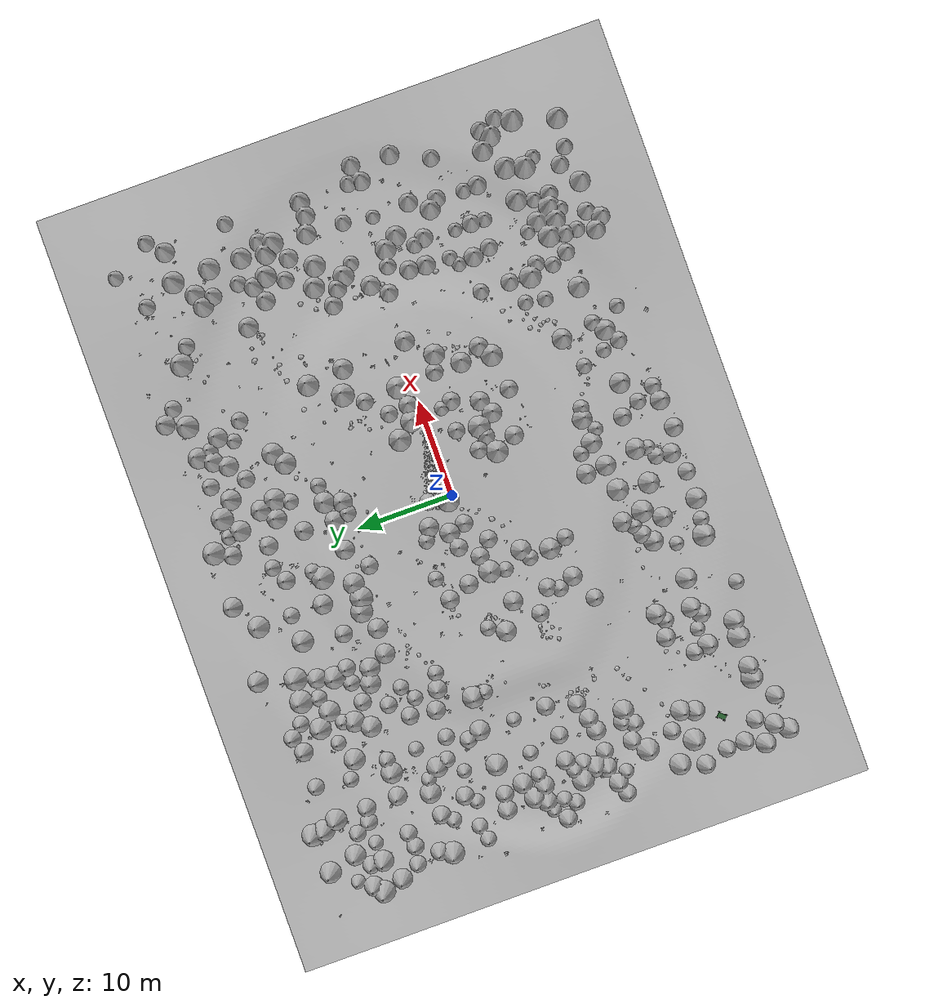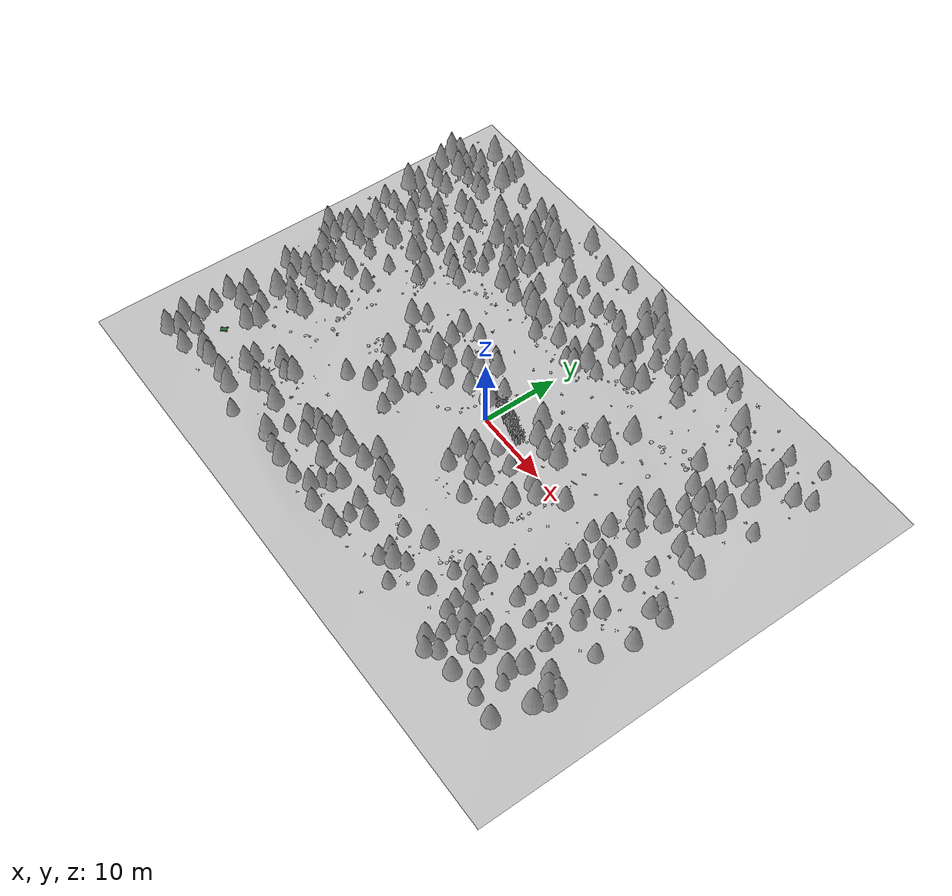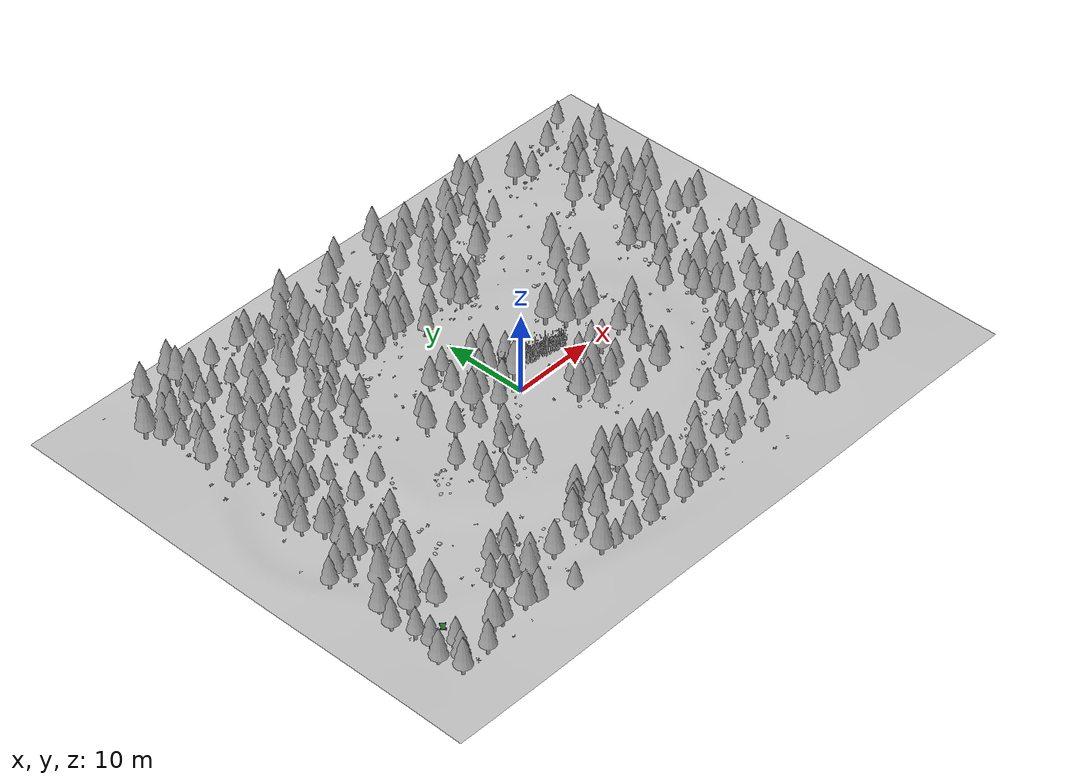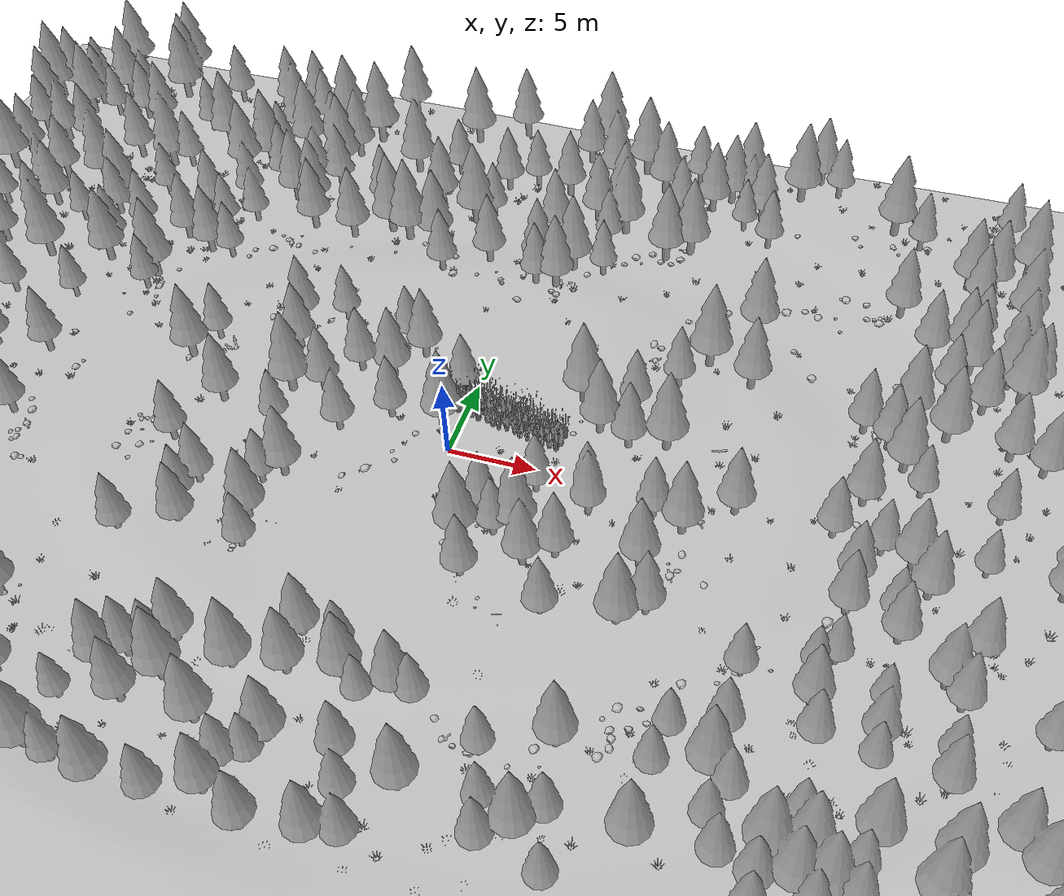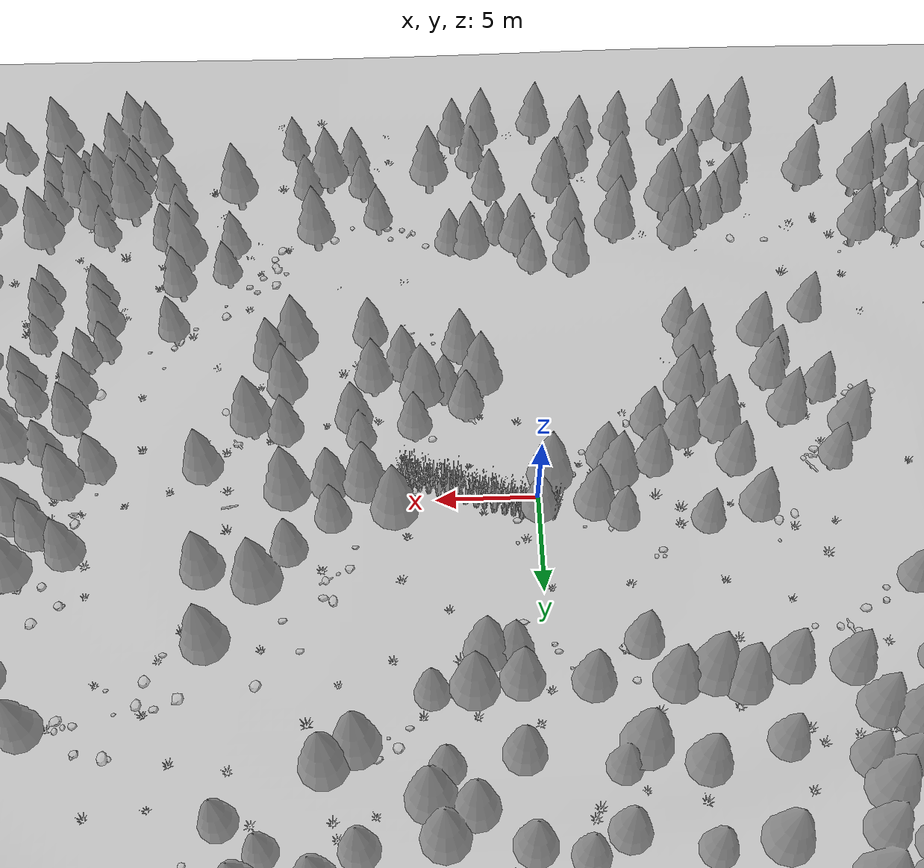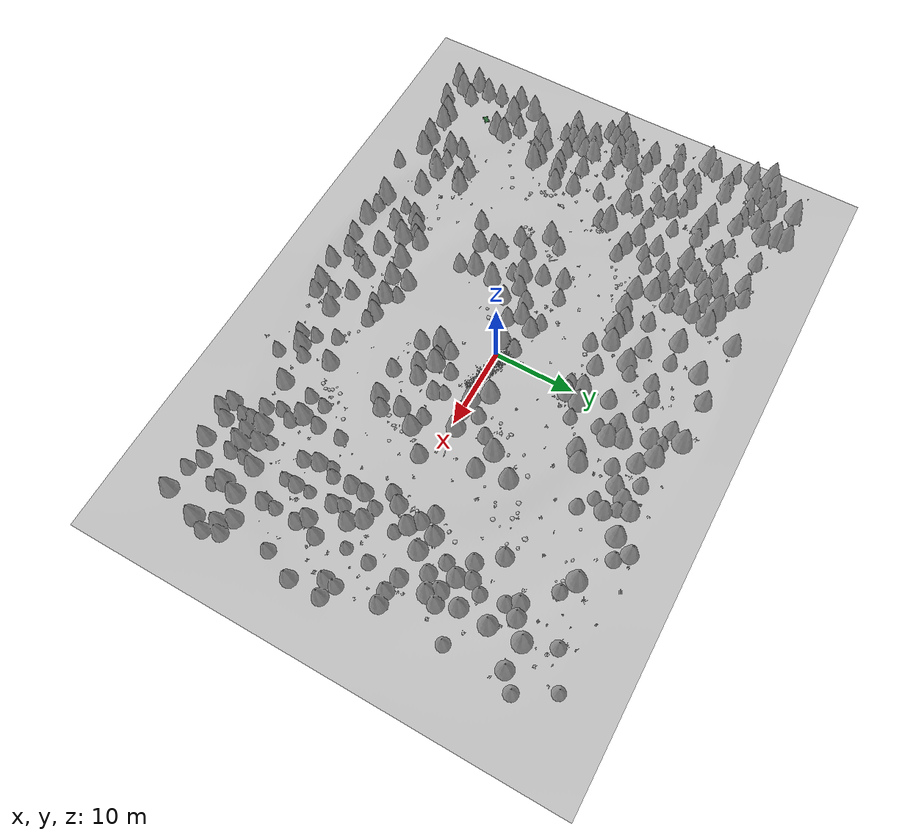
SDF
<?xml version='1.0' encoding='utf-8'?>
<sdf version="1.9">
  <world name="nomad_forest">
    <gravity>0 0 -9.81</gravity>
    <physics name="nomad_physics" type="ignored">
      <max_step_size>0.0016666666666666668</max_step_size>
      <real_time_factor>1</real_time_factor>
    </physics>
    <plugin filename="gz-sim-physics-system" name="gz::sim::systems::Physics" />
    <plugin filename="gz-sim-user-commands-system" name="gz::sim::systems::UserCommands" />
    <plugin filename="gz-sim-scene-broadcaster-system" name="gz::sim::systems::SceneBroadcaster" />
    <plugin filename="gz-sim-sensors-system" name="gz::sim::systems::Sensors">
      <render_engine>ogre2</render_engine>
    </plugin>
    <plugin filename="gz-sim-imu-system" name="gz::sim::systems::Imu" />
    <scene>
      <ambient>0.6 0.6 0.6 1</ambient>
      <background>0.62 0.75 0.86 1</background>
      <shadows>false</shadows>
    </scene>
    <light name="sun" type="directional">
      <pose>0 0 20 0 0 0</pose>
      <diffuse>0.8 0.8 0.8 1</diffuse>
      <specular>0.1 0.1 0.1 1</specular>
      <direction>-0.4 -0.2 -1</direction>
      <cast_shadows>false</cast_shadows>
    </light>
    <gui fullscreen="false">
      <plugin filename="MinimalScene" name="3D View">
        <gz-gui>
          <title>3D View</title>
          <property type="bool" key="showTitleBar">false</property>
          <property type="string" key="state">docked</property>
        </gz-gui>
        <engine>ogre2</engine>
        <scene>scene</scene>
        <ambient_light>0.6 0.6 0.6</ambient_light>
        <background_color>0.62 0.75 0.86</background_color>
        <camera_pose>-43 -38 48 0 0.70 0.72</camera_pose>
      </plugin>
      <plugin filename="GzSceneManager" name="GzSceneManager">
        <gz-gui>
          <property type="string" key="state">floating</property>
          <property type="bool" key="showTitleBar">false</property>
          <property type="bool" key="resizable">false</property>
          <property type="double" key="height">5</property>
          <property type="double" key="width">5</property>
        </gz-gui>
      </plugin>
      <plugin filename="InteractiveViewControl" name="InteractiveViewControl">
        <gz-gui>
          <property type="string" key="state">floating</property>
          <property type="bool" key="showTitleBar">false</property>
          <property type="bool" key="resizable">false</property>
          <property type="double" key="height">5</property>
          <property type="double" key="width">5</property>
        </gz-gui>
      </plugin>
      <plugin filename="CameraTracking" name="CameraTracking">
        <gz-gui>
          <property type="string" key="state">floating</property>
          <property type="bool" key="showTitleBar">false</property>
          <property type="bool" key="resizable">false</property>
          <property type="double" key="height">5</property>
          <property type="double" key="width">5</property>
        </gz-gui>
      </plugin>
      <plugin filename="EntityContextMenuPlugin" name="EntityContextMenuPlugin">
        <gz-gui>
          <property type="string" key="state">floating</property>
          <property type="bool" key="showTitleBar">false</property>
          <property type="bool" key="resizable">false</property>
          <property type="double" key="height">5</property>
          <property type="double" key="width">5</property>
        </gz-gui>
      </plugin>
      <plugin filename="SelectEntities" name="SelectEntities">
        <gz-gui>
          <property type="string" key="state">floating</property>
          <property type="bool" key="showTitleBar">false</property>
          <property type="bool" key="resizable">false</property>
          <property type="double" key="height">5</property>
          <property type="double" key="width">5</property>
        </gz-gui>
      </plugin>
      <plugin filename="WorldControl" name="WorldControl">
        <gz-gui>
          <property type="string" key="state">floating</property>
          <property type="bool" key="showTitleBar">false</property>
          <property type="bool" key="resizable">false</property>
          <property type="double" key="height">72</property>
          <property type="double" key="width">180</property>
          <property type="double" key="z">1</property>
          <anchors target="3D View">
            <line own="left" target="left" />
            <line own="bottom" target="bottom" />
          </anchors>
        </gz-gui>
        <play_pause>true</play_pause>
        <step>true</step>
        <start_paused>false</start_paused>
      </plugin>
      <plugin filename="WorldStats" name="WorldStats">
        <gz-gui>
          <property type="string" key="state">floating</property>
          <property type="bool" key="showTitleBar">false</property>
          <property type="bool" key="resizable">false</property>
          <property type="double" key="height">110</property>
          <property type="double" key="width">290</property>
          <property type="double" key="z">1</property>
          <anchors target="3D View">
            <line own="right" target="right" />
            <line own="bottom" target="bottom" />
          </anchors>
        </gz-gui>
        <sim_time>true</sim_time>
        <real_time>true</real_time>
        <real_time_factor>true</real_time_factor>
        <iterations>true</iterations>
      </plugin>
      <plugin filename="EntityTree" name="EntityTree">
        <gz-gui />
      </plugin>
      <plugin filename="ComponentInspector" name="ComponentInspector">
        <gz-gui />
      </plugin>
    </gui>
    <model name="terrain">
      <static>true</static>
      <pose>0 0 0 0 0 0</pose>
      <link name="link">
        <visual name="dirt_terrain">
          <geometry>
            <mesh>
              <uri>../assets/geometry/terrain.obj</uri>
            </mesh>
          </geometry>
        </visual>
        <collision name="terrain_collision">
          <geometry>
            <mesh>
              <uri>../assets/geometry/terrain.obj</uri>
            </mesh>
          </geometry>
        </collision>
      </link>
    </model>
    <model name="roadside_details">
      <static>true</static>
      <pose>0 0 0 0 0 0</pose>
      <link name="link">
        <visual name="visual_only">
          <geometry>
            <mesh>
              <uri>../assets/geometry/roadside_details.obj</uri>
            </mesh>
          </geometry>
        </visual>
      </link>
    </model>
    <model name="forest_far">
      <static>true</static>
      <pose>0 0 0 0 0 0</pose>
      <link name="link">
        <visual name="visual_only">
          <geometry>
            <mesh>
              <uri>../assets/geometry/forest_far.obj</uri>
            </mesh>
          </geometry>
        </visual>
      </link>
    </model>
    <model name="forest_grass">
      <static>true</static>
      <pose>0 0 0 0 0 0</pose>
      <link name="link">
        <visual name="visual_only">
          <geometry>
            <mesh>
              <uri>../assets/geometry/grass.obj</uri>
            </mesh>
          </geometry>
        </visual>
      </link>
    </model>
    <model name="path_grass">
      <static>true</static>
      <pose>0 0 0 0 0 0</pose>
      <link name="link">
        <visual name="visual_only">
          <geometry>
            <mesh>
              <uri>../assets/geometry/path_grass.obj</uri>
            </mesh>
          </geometry>
        </visual>
      </link>
    </model>
    <model name="meadow_grass">
      <static>true</static>
      <pose>0 0 0 0 0 0</pose>
      <link name="link">
        <visual name="visual_only">
          <geometry>
            <mesh>
              <uri>../assets/geometry/meadow_grass.obj</uri>
            </mesh>
          </geometry>
        </visual>
      </link>
    </model>
    <model name="tree_0000">
      <static>true</static>
      <pose>-32.226043951444034 -22.561121560247948 -0.09695232075887993 0 0 2.25313718157236</pose>
      <link name="link">
        <visual name="pine">
          <geometry>
            <mesh>
              <uri>../assets/models/pine_tree.obj</uri>
              <scale>1.1138156130767138 1.1138156130767138 1.1138156130767138</scale>
            </mesh>
          </geometry>
        </visual>
        <collision name="trunk">
          <pose>0 0 1.8656411519034957 0 0 0</pose>
          <geometry>
            <box>
              <size>0.44 0.44 3.7312823038069913</size>
            </box>
          </geometry>
        </collision>
      </link>
    </model>
    <model name="tree_0017">
      <static>true</static>
      <pose>-25.934130038540484 -22.030823622652274 0.17504397894948817 0 0 1.7514435841609088</pose>
      <link name="link">
        <visual name="pine">
          <geometry>
            <mesh>
              <uri>../assets/models/pine_tree.obj</uri>
              <scale>1.122600585121548 1.122600585121548 1.122600585121548</scale>
            </mesh>
          </geometry>
        </visual>
        <collision name="trunk">
          <pose>0 0 1.8803559800785927 0 0 0</pose>
          <geometry>
            <box>
              <size>0.44 0.44 3.7607119601571855</size>
            </box>
          </geometry>
        </collision>
      </link>
    </model>
    <model name="tree_0028">
      <static>true</static>
      <pose>-22.518766216160994 -18.9405773653081 0.15308021073727865 0 0 1.4262492252962382</pose>
      <link name="link">
        <visual name="pine">
          <geometry>
            <mesh>
              <uri>../assets/models/pine_tree.obj</uri>
              <scale>1.1458913713629457 1.1458913713629457 1.1458913713629457</scale>
            </mesh>
          </geometry>
        </visual>
        <collision name="trunk">
          <pose>0 0 1.9193680470329342 0 0 0</pose>
          <geometry>
            <box>
              <size>0.44 0.44 3.8387360940658684</size>
            </box>
          </geometry>
        </collision>
      </link>
    </model>
    <model name="tree_0029">
      <static>true</static>
      <pose>-22.48286110717729 -1.6471006049302637 3.0650650778708295 0 0 -1.3137019673913508</pose>
      <link name="link">
        <visual name="pine">
          <geometry>
            <mesh>
              <uri>../assets/models/pine_tree.obj</uri>
              <scale>1.0317757081542716 1.0317757081542716 1.0317757081542716</scale>
            </mesh>
          </geometry>
        </visual>
        <collision name="trunk">
          <pose>0 0 1.7282243111584048 0 0 0</pose>
          <geometry>
            <box>
              <size>0.44 0.44 3.4564486223168096</size>
            </box>
          </geometry>
        </collision>
      </link>
    </model>
    <model name="tree_0038">
      <static>true</static>
      <pose>-19.099051308219067 4.688584045351522 4.0956109040979305 0 0 1.0233060287015112</pose>
      <link name="link">
        <visual name="pine">
          <geometry>
            <mesh>
              <uri>../assets/models/pine_tree.obj</uri>
              <scale>1.2300304656711365 1.2300304656711365 1.2300304656711365</scale>
            </mesh>
          </geometry>
        </visual>
        <collision name="trunk">
          <pose>0 0 2.0603010299991538 0 0 0</pose>
          <geometry>
            <box>
              <size>0.44 0.44 4.1206020599983075</size>
            </box>
          </geometry>
        </collision>
      </link>
    </model>
    <model name="tree_0050">
      <static>true</static>
      <pose>-11.620429319413416 -8.597974119726413 -0.1385526412986445 0 0 1.7560091778610971</pose>
      <link name="link">
        <visual name="pine">
          <geometry>
            <mesh>
              <uri>../assets/models/pine_tree.obj</uri>
              <scale>1.0891174741979965 1.0891174741979965 1.0891174741979965</scale>
            </mesh>
          </geometry>
        </visual>
        <collision name="trunk">
          <pose>0 0 1.8242717692816441 0 0 0</pose>
          <geometry>
            <box>
              <size>0.44 0.44 3.6485435385632883</size>
            </box>
          </geometry>
        </collision>
      </link>
    </model>
    <model name="tree_0053">
      <static>true</static>
      <pose>-12.233607550173762 11.327495564412532 3.9964223456432064 0 0 -0.7573495232471299</pose>
      <link name="link">
        <visual name="pine">
          <geometry>
            <mesh>
              <uri>../assets/models/pine_tree.obj</uri>
              <scale>1.1085845054551755 1.1085845054551755 1.1085845054551755</scale>
            </mesh>
          </geometry>
        </visual>
        <collision name="trunk">
          <pose>0 0 1.856879046637419 0 0 0</pose>
          <geometry>
            <box>
              <size>0.44 0.44 3.713758093274838</size>
            </box>
          </geometry>
        </collision>
      </link>
    </model>
    <model name="tree_0065">
      <static>true</static>
      <pose>-5.019698506090619 -15.720630435875462 -0.07928766670003033 0 0 -0.7768563395972208</pose>
      <link name="link">
        <visual name="pine">
          <geometry>
            <mesh>
              <uri>../assets/models/pine_tree.obj</uri>
              <scale>1.243984195215945 1.243984195215945 1.243984195215945</scale>
            </mesh>
          </geometry>
        </visual>
        <collision name="trunk">
          <pose>0 0 2.0836735269867077 0 0 0</pose>
          <geometry>
            <box>
              <size>0.44 0.44 4.167347053973415</size>
            </box>
          </geometry>
        </collision>
      </link>
    </model>
    <model name="tree_0068">
      <static>true</static>
      <pose>-4.802965342162438 11.879200024307732 4.089483926855591 0 0 -1.357743328218155</pose>
      <link name="link">
        <visual name="pine">
          <geometry>
            <mesh>
              <uri>../assets/models/pine_tree.obj</uri>
              <scale>1.1766034608474223 1.1766034608474223 1.1766034608474223</scale>
            </mesh>
          </geometry>
        </visual>
        <collision name="trunk">
          <pose>0 0 1.9708107969194324 0 0 0</pose>
          <geometry>
            <box>
              <size>0.44 0.44 3.941621593838865</size>
            </box>
          </geometry>
        </collision>
      </link>
    </model>
    <model name="tree_0074">
      <static>true</static>
      <pose>-1.419795215101331 11.611543605977054 3.7308385244072015 0 0 -2.799157075199825</pose>
      <link name="link">
        <visual name="pine">
          <geometry>
            <mesh>
              <uri>../assets/models/pine_tree.obj</uri>
              <scale>1.0773390364673898 1.0773390364673898 1.0773390364673898</scale>
            </mesh>
          </geometry>
        </visual>
        <collision name="trunk">
          <pose>0 0 1.804542886082878 0 0 0</pose>
          <geometry>
            <box>
              <size>0.44 0.44 3.609085772165756</size>
            </box>
          </geometry>
        </collision>
      </link>
    </model>
    <model name="tree_0079">
      <static>true</static>
      <pose>1.4040343907407518 -15.725831270517384 -0.10772524546870592 0 0 -2.392526844625827</pose>
      <link name="link">
        <visual name="pine">
          <geometry>
            <mesh>
              <uri>../assets/models/pine_tree.obj</uri>
              <scale>0.8603425744427444 0.8603425744427444 0.8603425744427444</scale>
            </mesh>
          </geometry>
        </visual>
        <collision name="trunk">
          <pose>0 0 1.441073812191597 0 0 0</pose>
          <geometry>
            <box>
              <size>0.44 0.44 2.882147624383194</size>
            </box>
          </geometry>
        </collision>
      </link>
    </model>
    <model name="tree_0085">
      <static>true</static>
      <pose>4.414682843560055 -5.172826575479321 0.7079076270196714 0 0 2.240257303027585</pose>
      <link name="link">
        <visual name="pine">
          <geometry>
            <mesh>
              <uri>../assets/models/pine_tree.obj</uri>
              <scale>0.9675177079361967 0.9675177079361967 0.9675177079361967</scale>
            </mesh>
          </geometry>
        </visual>
        <collision name="trunk">
          <pose>0 0 1.6205921607931295 0 0 0</pose>
          <geometry>
            <box>
              <size>0.44 0.44 3.241184321586259</size>
            </box>
          </geometry>
        </collision>
      </link>
    </model>
    <model name="tree_0090">
      <static>true</static>
      <pose>8.09205933031451 -8.909802457598419 0.16759876982480915 0 0 0.543151040963163</pose>
      <link name="link">
        <visual name="pine">
          <geometry>
            <mesh>
              <uri>../assets/models/pine_tree.obj</uri>
              <scale>1.0219804891328 1.0219804891328 1.0219804891328</scale>
            </mesh>
          </geometry>
        </visual>
        <collision name="trunk">
          <pose>0 0 1.71181731929744 0 0 0</pose>
          <geometry>
            <box>
              <size>0.44 0.44 3.42363463859488</size>
            </box>
          </geometry>
        </collision>
      </link>
    </model>
    <model name="tree_0093">
      <static>true</static>
      <pose>8.166608384932596 1.3395274352616688 2.748387835904799 0 0 -1.0150078506163611</pose>
      <link name="link">
        <visual name="pine">
          <geometry>
            <mesh>
              <uri>../assets/models/pine_tree.obj</uri>
              <scale>1.180015492979234 1.180015492979234 1.180015492979234</scale>
            </mesh>
          </geometry>
        </visual>
        <collision name="trunk">
          <pose>0 0 1.9765259507402169 0 0 0</pose>
          <geometry>
            <box>
              <size>0.44 0.44 3.9530519014804337</size>
            </box>
          </geometry>
        </collision>
      </link>
    </model>
    <model name="tree_0097">
      <static>true</static>
      <pose>12.103327871964035 -5.279304053281655 1.0596436875109276 0 0 2.910441953926141</pose>
      <link name="link">
        <visual name="pine">
          <geometry>
            <mesh>
              <uri>../assets/models/pine_tree.obj</uri>
              <scale>1.1519023268321797 1.1519023268321797 1.1519023268321797</scale>
            </mesh>
          </geometry>
        </visual>
        <collision name="trunk">
          <pose>0 0 1.929436397443901 0 0 0</pose>
          <geometry>
            <box>
              <size>0.44 0.44 3.858872794887802</size>
            </box>
          </geometry>
        </collision>
      </link>
    </model>
    <model name="tree_0101">
      <static>true</static>
      <pose>12.17791697907382 18.211576002194043 3.970718524714318 0 0 1.8452593733793228</pose>
      <link name="link">
        <visual name="pine">
          <geometry>
            <mesh>
              <uri>../assets/models/pine_tree.obj</uri>
              <scale>0.8381686725403245 0.8381686725403245 0.8381686725403245</scale>
            </mesh>
          </geometry>
        </visual>
        <collision name="trunk">
          <pose>0 0 1.4039325265050435 0 0 0</pose>
          <geometry>
            <box>
              <size>0.44 0.44 2.807865053010087</size>
            </box>
          </geometry>
        </collision>
      </link>
    </model>
    <model name="tree_0108">
      <static>true</static>
      <pose>18.067166668847747 -12.598020962311223 0.052352232862963775 0 0 -3.0305764284153707</pose>
      <link name="link">
        <visual name="pine">
          <geometry>
            <mesh>
              <uri>../assets/models/pine_tree.obj</uri>
              <scale>1.0039759624250735 1.0039759624250735 1.0039759624250735</scale>
            </mesh>
          </geometry>
        </visual>
        <collision name="trunk">
          <pose>0 0 1.6816597370619981 0 0 0</pose>
          <geometry>
            <box>
              <size>0.44 0.44 3.3633194741239962</size>
            </box>
          </geometry>
        </collision>
      </link>
    </model>
    <model name="tree_0113">
      <static>true</static>
      <pose>21.43584275141814 -8.440225477670785 0.40124177072812606 0 0 -2.4944077020631195</pose>
      <link name="link">
        <visual name="pine">
          <geometry>
            <mesh>
              <uri>../assets/models/pine_tree.obj</uri>
              <scale>0.8184855919871812 0.8184855919871812 0.8184855919871812</scale>
            </mesh>
          </geometry>
        </visual>
        <collision name="trunk">
          <pose>0 0 1.3709633665785286 0 0 0</pose>
          <geometry>
            <box>
              <size>0.44 0.44 2.741926733157057</size>
            </box>
          </geometry>
        </collision>
      </link>
    </model>
    <model name="tree_0123">
      <static>true</static>
      <pose>25.254457430298633 8.203424454333309 3.788328063644859 0 0 3.0451428287578173</pose>
      <link name="link">
        <visual name="pine">
          <geometry>
            <mesh>
              <uri>../assets/models/pine_tree.obj</uri>
              <scale>0.9626912353876398 0.9626912353876398 0.9626912353876398</scale>
            </mesh>
          </geometry>
        </visual>
        <collision name="trunk">
          <pose>0 0 1.6125078192742968 0 0 0</pose>
          <geometry>
            <box>
              <size>0.44 0.44 3.2250156385485935</size>
            </box>
          </geometry>
        </collision>
      </link>
    </model>
    <model name="tree_0124">
      <static>true</static>
      <pose>25.61315934582009 11.318399117828445 3.87919084352 0 0 1.8800140066571884</pose>
      <link name="link">
        <visual name="pine">
          <geometry>
            <mesh>
              <uri>../assets/models/pine_tree.obj</uri>
              <scale>1.0703302634881893 1.0703302634881893 1.0703302634881893</scale>
            </mesh>
          </geometry>
        </visual>
        <collision name="trunk">
          <pose>0 0 1.7928031913427172 0 0 0</pose>
          <geometry>
            <box>
              <size>0.44 0.44 3.5856063826854343</size>
            </box>
          </geometry>
        </collision>
      </link>
    </model>
    <model name="tree_0145">
      <static>true</static>
      <pose>1.844830629709577 10.1728805533047 4.064830334963324 0 0 0.7859794770549072</pose>
      <link name="link">
        <visual name="pine">
          <geometry>
            <mesh>
              <uri>../assets/models/pine_tree.obj</uri>
              <scale>0.9685998039980167 0.9685998039980167 0.9685998039980167</scale>
            </mesh>
          </geometry>
        </visual>
        <collision name="trunk">
          <pose>0 0 1.622404671696678 0 0 0</pose>
          <geometry>
            <box>
              <size>0.44 0.44 3.244809343393356</size>
            </box>
          </geometry>
        </collision>
      </link>
    </model>
    <model name="tree_0147">
      <static>true</static>
      <pose>7.70764392117114 -16.780587005585012 0.03342473015368693 0 0 -2.4795058111798234</pose>
      <link name="link">
        <visual name="pine">
          <geometry>
            <mesh>
              <uri>../assets/models/pine_tree.obj</uri>
              <scale>0.885928341494171 0.885928341494171 0.885928341494171</scale>
            </mesh>
          </geometry>
        </visual>
        <collision name="trunk">
          <pose>0 0 1.4839299720027364 0 0 0</pose>
          <geometry>
            <box>
              <size>0.44 0.44 2.9678599440054727</size>
            </box>
          </geometry>
        </collision>
      </link>
    </model>
    <model name="tree_0152">
      <static>true</static>
      <pose>18.13207483502385 -9.57056188500926 0.32670338482310907 0 0 2.345931137766924</pose>
      <link name="link">
        <visual name="pine">
          <geometry>
            <mesh>
              <uri>../assets/models/pine_tree.obj</uri>
              <scale>0.9186525355624718 0.9186525355624718 0.9186525355624718</scale>
            </mesh>
          </geometry>
        </visual>
        <collision name="trunk">
          <pose>0 0 1.5387429970671405 0 0 0</pose>
          <geometry>
            <box>
              <size>0.44 0.44 3.077485994134281</size>
            </box>
          </geometry>
        </collision>
      </link>
    </model>
    <model name="tree_0153">
      <static>true</static>
      <pose>2.785083350919912 -14.783711985202673 -0.20294977764239625 0 0 -0.6714789105508467</pose>
      <link name="link">
        <visual name="pine">
          <geometry>
            <mesh>
              <uri>../assets/models/pine_tree.obj</uri>
              <scale>1.1348528074091004 1.1348528074091004 1.1348528074091004</scale>
            </mesh>
          </geometry>
        </visual>
        <collision name="trunk">
          <pose>0 0 1.9008784524102433 0 0 0</pose>
          <geometry>
            <box>
              <size>0.44 0.44 3.8017569048204867</size>
            </box>
          </geometry>
        </collision>
      </link>
    </model>
    <model name="tree_0154">
      <static>true</static>
      <pose>-6.356132521814708 11.636028037471846 4.233290636250082 0 0 1.931778694469644</pose>
      <link name="link">
        <visual name="pine">
          <geometry>
            <mesh>
              <uri>../assets/models/pine_tree.obj</uri>
              <scale>1.2707191312738144 1.2707191312738144 1.2707191312738144</scale>
            </mesh>
          </geometry>
        </visual>
        <collision name="trunk">
          <pose>0 0 2.128454544883639 0 0 0</pose>
          <geometry>
            <box>
              <size>0.44 0.44 4.256909089767278</size>
            </box>
          </geometry>
        </collision>
      </link>
    </model>
    <model name="tree_0160">
      <static>true</static>
      <pose>-9.685070749091384 11.182210165610456 3.983878141788043 0 0 0.7946107344376528</pose>
      <link name="link">
        <visual name="pine">
          <geometry>
            <mesh>
              <uri>../assets/models/pine_tree.obj</uri>
              <scale>1.1105706846773957 1.1105706846773957 1.1105706846773957</scale>
            </mesh>
          </geometry>
        </visual>
        <collision name="trunk">
          <pose>0 0 1.860205896834638 0 0 0</pose>
          <geometry>
            <box>
              <size>0.44 0.44 3.720411793669276</size>
            </box>
          </geometry>
        </collision>
      </link>
    </model>
    <model name="tree_0163">
      <static>true</static>
      <pose>-17.958381655505868 -15.129194381648817 0.029776809875019673 0 0 -2.6073345384654654</pose>
      <link name="link">
        <visual name="pine">
          <geometry>
            <mesh>
              <uri>../assets/models/pine_tree.obj</uri>
              <scale>1.151262795606962 1.151262795606962 1.151262795606962</scale>
            </mesh>
          </geometry>
        </visual>
        <collision name="trunk">
          <pose>0 0 1.9283651826416615 0 0 0</pose>
          <geometry>
            <box>
              <size>0.44 0.44 3.856730365283323</size>
            </box>
          </geometry>
        </collision>
      </link>
    </model>
    <model name="tree_0165">
      <static>true</static>
      <pose>-29.54834840482915 -23.55740282877368 0.035276795590797314 0 0 -1.3106274725579228</pose>
      <link name="link">
        <visual name="pine">
          <geometry>
            <mesh>
              <uri>../assets/models/pine_tree.obj</uri>
              <scale>1.0537103158486423 1.0537103158486423 1.0537103158486423</scale>
            </mesh>
          </geometry>
        </visual>
        <collision name="trunk">
          <pose>0 0 1.7649647790464758 0 0 0</pose>
          <geometry>
            <box>
              <size>0.44 0.44 3.5299295580929515</size>
            </box>
          </geometry>
        </collision>
      </link>
    </model>
    <model name="tree_0176">
      <static>true</static>
      <pose>15.652497003100407 -13.418253456045443 -0.05930626893724187 0 0 -1.4276371842760884</pose>
      <link name="link">
        <visual name="pine">
          <geometry>
            <mesh>
              <uri>../assets/models/pine_tree.obj</uri>
              <scale>0.8751090141221561 0.8751090141221561 0.8751090141221561</scale>
            </mesh>
          </geometry>
        </visual>
        <collision name="trunk">
          <pose>0 0 1.4658075986546115 0 0 0</pose>
          <geometry>
            <box>
              <size>0.44 0.44 2.931615197309223</size>
            </box>
          </geometry>
        </collision>
      </link>
    </model>
    <model name="tree_0183">
      <static>true</static>
      <pose>-28.33708616124009 -15.521181229560044 -0.13074560218709894 0 0 -2.6840625660481088</pose>
      <link name="link">
        <visual name="pine">
          <geometry>
            <mesh>
              <uri>../assets/models/pine_tree.obj</uri>
              <scale>1.1496535405558723 1.1496535405558723 1.1496535405558723</scale>
            </mesh>
          </geometry>
        </visual>
        <collision name="trunk">
          <pose>0 0 1.9256696804310862 0 0 0</pose>
          <geometry>
            <box>
              <size>0.44 0.44 3.8513393608621724</size>
            </box>
          </geometry>
        </collision>
      </link>
    </model>
    <model name="tree_0186">
      <static>true</static>
      <pose>-27.824025412930695 -14.181672228153468 -0.02799506630359654 0 0 1.7086709303909975</pose>
      <link name="link">
        <visual name="pine">
          <geometry>
            <mesh>
              <uri>../assets/models/pine_tree.obj</uri>
              <scale>1.1714612942632079 1.1714612942632079 1.1714612942632079</scale>
            </mesh>
          </geometry>
        </visual>
        <collision name="trunk">
          <pose>0 0 1.9621976678908732 0 0 0</pose>
          <geometry>
            <box>
              <size>0.44 0.44 3.9243953357817465</size>
            </box>
          </geometry>
        </collision>
      </link>
    </model>
    <model name="tree_0190">
      <static>true</static>
      <pose>8.440680881386108 14.199549724739121 4.102833950101345 0 0 -2.826538755678515</pose>
      <link name="link">
        <visual name="pine">
          <geometry>
            <mesh>
              <uri>../assets/models/pine_tree.obj</uri>
              <scale>1.201619926565681 1.201619926565681 1.201619926565681</scale>
            </mesh>
          </geometry>
        </visual>
        <collision name="trunk">
          <pose>0 0 2.0127133769975156 0 0 0</pose>
          <geometry>
            <box>
              <size>0.44 0.44 4.025426753995031</size>
            </box>
          </geometry>
        </collision>
      </link>
    </model>
    <model name="tree_0191">
      <static>true</static>
      <pose>3.8818119574392824 -15.08116833013731 -0.1290276752715569 0 0 -2.3627623723663453</pose>
      <link name="link">
        <visual name="pine">
          <geometry>
            <mesh>
              <uri>../assets/models/pine_tree.obj</uri>
              <scale>0.917618205168787 0.917618205168787 0.917618205168787</scale>
            </mesh>
          </geometry>
        </visual>
        <collision name="trunk">
          <pose>0 0 1.5370104936577182 0 0 0</pose>
          <geometry>
            <box>
              <size>0.44 0.44 3.0740209873154365</size>
            </box>
          </geometry>
        </collision>
      </link>
    </model>
    <model name="tree_0192">
      <static>true</static>
      <pose>22.435816932964407 -3.536446098520699 1.346411810773645 0 0 2.1371616142582996</pose>
      <link name="link">
        <visual name="pine">
          <geometry>
            <mesh>
              <uri>../assets/models/pine_tree.obj</uri>
              <scale>1.0605517183830016 1.0605517183830016 1.0605517183830016</scale>
            </mesh>
          </geometry>
        </visual>
        <collision name="trunk">
          <pose>0 0 1.7764241282915276 0 0 0</pose>
          <geometry>
            <box>
              <size>0.44 0.44 3.5528482565830553</size>
            </box>
          </geometry>
        </collision>
      </link>
    </model>
    <model name="tree_0193">
      <static>true</static>
      <pose>-33.74157899140322 -14.775898882507773 -0.0014158623533813532 0 0 2.1563151794078284</pose>
      <link name="link">
        <visual name="pine">
          <geometry>
            <mesh>
              <uri>../assets/models/pine_tree.obj</uri>
              <scale>1.0817096314764492 1.0817096314764492 1.0817096314764492</scale>
            </mesh>
          </geometry>
        </visual>
        <collision name="trunk">
          <pose>0 0 1.8118636327230524 0 0 0</pose>
          <geometry>
            <box>
              <size>0.44 0.44 3.623727265446105</size>
            </box>
          </geometry>
        </collision>
      </link>
    </model>
    <model name="tree_0199">
      <static>true</static>
      <pose>23.569982557056683 5.795406408614738 3.7865020065337056 0 0 -1.623077768715212</pose>
      <link name="link">
        <visual name="pine">
          <geometry>
            <mesh>
              <uri>../assets/models/pine_tree.obj</uri>
              <scale>1.1845048146195674 1.1845048146195674 1.1845048146195674</scale>
            </mesh>
          </geometry>
        </visual>
        <collision name="trunk">
          <pose>0 0 1.9840455644877755 0 0 0</pose>
          <geometry>
            <box>
              <size>0.44 0.44 3.968091128975551</size>
            </box>
          </geometry>
        </collision>
      </link>
    </model>
    <model name="tree_0200">
      <static>true</static>
      <pose>-11.037143985253817 -17.338721346189022 -0.007577509590215678 0 0 -1.5973402352282648</pose>
      <link name="link">
        <visual name="pine">
          <geometry>
            <mesh>
              <uri>../assets/models/pine_tree.obj</uri>
              <scale>1.158121903623571 1.158121903623571 1.158121903623571</scale>
            </mesh>
          </geometry>
        </visual>
        <collision name="trunk">
          <pose>0 0 1.9398541885694816 0 0 0</pose>
          <geometry>
            <box>
              <size>0.44 0.44 3.879708377138963</size>
            </box>
          </geometry>
        </collision>
      </link>
    </model>
    <model name="tree_0202">
      <static>true</static>
      <pose>6.818876670600538 2.955340465860676 3.08595945672692 0 0 1.0715975330827785</pose>
      <link name="link">
        <visual name="pine">
          <geometry>
            <mesh>
              <uri>../assets/models/pine_tree.obj</uri>
              <scale>1.2477985433231338 1.2477985433231338 1.2477985433231338</scale>
            </mesh>
          </geometry>
        </visual>
        <collision name="trunk">
          <pose>0 0 2.090062560066249 0 0 0</pose>
          <geometry>
            <box>
              <size>0.44 0.44 4.180125120132498</size>
            </box>
          </geometry>
        </collision>
      </link>
    </model>
    <model name="tree_0204">
      <static>true</static>
      <pose>-3.3389950961844974 3.8438912418582234 3.911891913505878 0 0 -2.9592714107791727</pose>
      <link name="link">
        <visual name="pine">
          <geometry>
            <mesh>
              <uri>../assets/models/pine_tree.obj</uri>
              <scale>0.8801866071895028 0.8801866071895028 0.8801866071895028</scale>
            </mesh>
          </geometry>
        </visual>
        <collision name="trunk">
          <pose>0 0 1.4743125670424173 0 0 0</pose>
          <geometry>
            <box>
              <size>0.44 0.44 2.9486251340848346</size>
            </box>
          </geometry>
        </collision>
      </link>
    </model>
    <model name="tree_0207">
      <static>true</static>
      <pose>3.5635179544175912 11.891871235077623 4.09328042839558 0 0 -2.9128157570038646</pose>
      <link name="link">
        <visual name="pine">
          <geometry>
            <mesh>
              <uri>../assets/models/pine_tree.obj</uri>
              <scale>1.185919274044591 1.185919274044591 1.185919274044591</scale>
            </mesh>
          </geometry>
        </visual>
        <collision name="trunk">
          <pose>0 0 1.98641478402469 0 0 0</pose>
          <geometry>
            <box>
              <size>0.44 0.44 3.97282956804938</size>
            </box>
          </geometry>
        </collision>
      </link>
    </model>
    <model name="tree_0209">
      <static>true</static>
      <pose>-0.43311243746486383 -13.53719587955047 0.19574211197388516 0 0 -3.0527752157441417</pose>
      <link name="link">
        <visual name="pine">
          <geometry>
            <mesh>
              <uri>../assets/models/pine_tree.obj</uri>
              <scale>0.8893685772365396 0.8893685772365396 0.8893685772365396</scale>
            </mesh>
          </geometry>
        </visual>
        <collision name="trunk">
          <pose>0 0 1.4896923668712039 0 0 0</pose>
          <geometry>
            <box>
              <size>0.44 0.44 2.9793847337424078</size>
            </box>
          </geometry>
        </collision>
      </link>
    </model>
    <model name="tree_0211">
      <static>true</static>
      <pose>0.23170583911337417 2.4392160301378816 2.2795953564710976 0 0 2.7915316872537828</pose>
      <link name="link">
        <visual name="pine">
          <geometry>
            <mesh>
              <uri>../assets/models/pine_tree.obj</uri>
              <scale>0.9595932818431513 0.9595932818431513 0.9595932818431513</scale>
            </mesh>
          </geometry>
        </visual>
        <collision name="trunk">
          <pose>0 0 1.6073187470872785 0 0 0</pose>
          <geometry>
            <box>
              <size>0.44 0.44 3.214637494174557</size>
            </box>
          </geometry>
        </collision>
      </link>
    </model>
    <model name="tree_0216">
      <static>true</static>
      <pose>13.029466758064487 -7.4994979961646635 0.40771615344331275 0 0 -0.6609565583672433</pose>
      <link name="link">
        <visual name="pine">
          <geometry>
            <mesh>
              <uri>../assets/models/pine_tree.obj</uri>
              <scale>1.0804515140659818 1.0804515140659818 1.0804515140659818</scale>
            </mesh>
          </geometry>
        </visual>
        <collision name="trunk">
          <pose>0 0 1.8097562860605196 0 0 0</pose>
          <geometry>
            <box>
              <size>0.44 0.44 3.6195125721210393</size>
            </box>
          </geometry>
        </collision>
      </link>
    </model>
    <model name="tree_0218">
      <static>true</static>
      <pose>22.10161639404886 0.5635710988927869 2.3896555517212064 0 0 0.5925242542972715</pose>
      <link name="link">
        <visual name="pine">
          <geometry>
            <mesh>
              <uri>../assets/models/pine_tree.obj</uri>
              <scale>1.1020363064766003 1.1020363064766003 1.1020363064766003</scale>
            </mesh>
          </geometry>
        </visual>
        <collision name="trunk">
          <pose>0 0 1.8459108133483055 0 0 0</pose>
          <geometry>
            <box>
              <size>0.44 0.44 3.691821626696611</size>
            </box>
          </geometry>
        </collision>
      </link>
    </model>
    <model name="tree_0219">
      <static>true</static>
      <pose>5.891831122757075 -2.566269529153974 1.616724829270093 0 0 2.428343281246423</pose>
      <link name="link">
        <visual name="pine">
          <geometry>
            <mesh>
              <uri>../assets/models/pine_tree.obj</uri>
              <scale>0.9507468448184051 0.9507468448184051 0.9507468448184051</scale>
            </mesh>
          </geometry>
        </visual>
        <collision name="trunk">
          <pose>0 0 1.5925009650708286 0 0 0</pose>
          <geometry>
            <box>
              <size>0.44 0.44 3.1850019301416572</size>
            </box>
          </geometry>
        </collision>
      </link>
    </model>
    <model name="tree_0220">
      <static>true</static>
      <pose>5.319717613181496 11.940313679931393 4.067910813380731 0 0 1.4278087269920006</pose>
      <link name="link">
        <visual name="pine">
          <geometry>
            <mesh>
              <uri>../assets/models/pine_tree.obj</uri>
              <scale>0.8781726028357063 0.8781726028357063 0.8781726028357063</scale>
            </mesh>
          </geometry>
        </visual>
        <collision name="trunk">
          <pose>0 0 1.4709391097498081 0 0 0</pose>
          <geometry>
            <box>
              <size>0.44 0.44 2.9418782194996163</size>
            </box>
          </geometry>
        </collision>
      </link>
    </model>
    <model name="tree_0221">
      <static>true</static>
      <pose>-0.3782302625781142 0.5293858316961568 1.4946406064991107 0 0 2.572516854966049</pose>
      <link name="link">
        <visual name="pine">
          <geometry>
            <mesh>
              <uri>../assets/models/pine_tree.obj</uri>
              <scale>1.2361105122484934 1.2361105122484934 1.2361105122484934</scale>
            </mesh>
          </geometry>
        </visual>
        <collision name="trunk">
          <pose>0 0 2.0704851080162268 0 0 0</pose>
          <geometry>
            <box>
              <size>0.44 0.44 4.1409702160324535</size>
            </box>
          </geometry>
        </collision>
      </link>
    </model>
    <model name="tree_0223">
      <static>true</static>
      <pose>3.5714122232063303 -7.847086014846624 0.2693950579100194 0 0 1.6739985761373477</pose>
      <link name="link">
        <visual name="pine">
          <geometry>
            <mesh>
              <uri>../assets/models/pine_tree.obj</uri>
              <scale>1.0687225007619128 1.0687225007619128 1.0687225007619128</scale>
            </mesh>
          </geometry>
        </visual>
        <collision name="trunk">
          <pose>0 0 1.7901101887762039 0 0 0</pose>
          <geometry>
            <box>
              <size>0.44 0.44 3.5802203775524077</size>
            </box>
          </geometry>
        </collision>
      </link>
    </model>
    <model name="tree_0229">
      <static>true</static>
      <pose>-32.88872304252759 -19.18450726880608 -0.0003221194657796545 0 0 -1.7573053295900034</pose>
      <link name="link">
        <visual name="pine">
          <geometry>
            <mesh>
              <uri>../assets/models/pine_tree.obj</uri>
              <scale>1.066333219316281 1.066333219316281 1.066333219316281</scale>
            </mesh>
          </geometry>
        </visual>
        <collision name="trunk">
          <pose>0 0 1.7861081423547704 0 0 0</pose>
          <geometry>
            <box>
              <size>0.44 0.44 3.572216284709541</size>
            </box>
          </geometry>
        </collision>
      </link>
    </model>
    <model name="tree_0230">
      <static>true</static>
      <pose>21.39960197455943 4.632279396975946 3.287060660100178 0 0 -2.0843220529009114</pose>
      <link name="link">
        <visual name="pine">
          <geometry>
            <mesh>
              <uri>../assets/models/pine_tree.obj</uri>
              <scale>1.0340336623659456 1.0340336623659456 1.0340336623659456</scale>
            </mesh>
          </geometry>
        </visual>
        <collision name="trunk">
          <pose>0 0 1.732006384462959 0 0 0</pose>
          <geometry>
            <box>
              <size>0.44 0.44 3.464012768925918</size>
            </box>
          </geometry>
        </collision>
      </link>
    </model>
    <model name="tree_0231">
      <static>true</static>
      <pose>3.3841151539106704 -4.038452106920012 0.9304253747921445 0 0 1.4754345514062956</pose>
      <link name="link">
        <visual name="pine">
          <geometry>
            <mesh>
              <uri>../assets/models/pine_tree.obj</uri>
              <scale>0.9932701134580739 0.9932701134580739 0.9932701134580739</scale>
            </mesh>
          </geometry>
        </visual>
        <collision name="trunk">
          <pose>0 0 1.663727440042274 0 0 0</pose>
          <geometry>
            <box>
              <size>0.44 0.44 3.327454880084548</size>
            </box>
          </geometry>
        </collision>
      </link>
    </model>
    <model name="tree_0233">
      <static>true</static>
      <pose>14.780305708815014 9.543903860115101 4.154753917612376 0 0 -1.4580217669477222</pose>
      <link name="link">
        <visual name="pine">
          <geometry>
            <mesh>
              <uri>../assets/models/pine_tree.obj</uri>
              <scale>1.1969696393819989 1.1969696393819989 1.1969696393819989</scale>
            </mesh>
          </geometry>
        </visual>
        <collision name="trunk">
          <pose>0 0 2.004924145964848 0 0 0</pose>
          <geometry>
            <box>
              <size>0.44 0.44 4.009848291929696</size>
            </box>
          </geometry>
        </collision>
      </link>
    </model>
    <model name="tree_0235">
      <static>true</static>
      <pose>3.0101047278970157 10.27434312915831 4.030941822416165 0 0 -1.0240197977516978</pose>
      <link name="link">
        <visual name="pine">
          <geometry>
            <mesh>
              <uri>../assets/models/pine_tree.obj</uri>
              <scale>1.1353460595144083 1.1353460595144083 1.1353460595144083</scale>
            </mesh>
          </geometry>
        </visual>
        <collision name="trunk">
          <pose>0 0 1.9017046496866339 0 0 0</pose>
          <geometry>
            <box>
              <size>0.44 0.44 3.8034092993732678</size>
            </box>
          </geometry>
        </collision>
      </link>
    </model>
    <model name="tree_0242">
      <static>true</static>
      <pose>20.802842096223173 20.43855171849893 3.902659529358883 0 0 0.08687755394423444</pose>
      <link name="link">
        <visual name="pine">
          <geometry>
            <mesh>
              <uri>../assets/models/pine_tree.obj</uri>
              <scale>1.2754019106847523 1.2754019106847523 1.2754019106847523</scale>
            </mesh>
          </geometry>
        </visual>
        <collision name="trunk">
          <pose>0 0 2.13629820039696 0 0 0</pose>
          <geometry>
            <box>
              <size>0.44 0.44 4.27259640079392</size>
            </box>
          </geometry>
        </collision>
      </link>
    </model>
    <model name="tree_0245">
      <static>true</static>
      <pose>-9.437991093163316 3.610705145024802 3.9919677319809694 0 0 -0.5357036927552802</pose>
      <link name="link">
        <visual name="pine">
          <geometry>
            <mesh>
              <uri>../assets/models/pine_tree.obj</uri>
              <scale>1.039374079630504 1.039374079630504 1.039374079630504</scale>
            </mesh>
          </geometry>
        </visual>
        <collision name="trunk">
          <pose>0 0 1.7409515833810942 0 0 0</pose>
          <geometry>
            <box>
              <size>0.44 0.44 3.4819031667621885</size>
            </box>
          </geometry>
        </collision>
      </link>
    </model>
    <model name="tree_0247">
      <static>true</static>
      <pose>0.2525014534112273 -14.832146084386185 0.06953143166794434 0 0 -2.6069408954723325</pose>
      <link name="link">
        <visual name="pine">
          <geometry>
            <mesh>
              <uri>../assets/models/pine_tree.obj</uri>
              <scale>1.174752536826116 1.174752536826116 1.174752536826116</scale>
            </mesh>
          </geometry>
        </visual>
        <collision name="trunk">
          <pose>0 0 1.9677104991837444 0 0 0</pose>
          <geometry>
            <box>
              <size>0.44 0.44 3.935420998367489</size>
            </box>
          </geometry>
        </collision>
      </link>
    </model>
    <model name="tree_0248">
      <static>true</static>
      <pose>26.067117828825097 15.357716949064333 4.028278780778664 0 0 -0.9195605044671925</pose>
      <link name="link">
        <visual name="pine">
          <geometry>
            <mesh>
              <uri>../assets/models/pine_tree.obj</uri>
              <scale>0.9984800122995259 0.9984800122995259 0.9984800122995259</scale>
            </mesh>
          </geometry>
        </visual>
        <collision name="trunk">
          <pose>0 0 1.6724540206017058 0 0 0</pose>
          <geometry>
            <box>
              <size>0.44 0.44 3.3449080412034116</size>
            </box>
          </geometry>
        </collision>
      </link>
    </model>
    <model name="tree_0249">
      <static>true</static>
      <pose>26.434689671457306 12.63227326625347 3.880101167758681 0 0 2.9395098139307043</pose>
      <link name="link">
        <visual name="pine">
          <geometry>
            <mesh>
              <uri>../assets/models/pine_tree.obj</uri>
              <scale>0.9201905774272329 0.9201905774272329 0.9201905774272329</scale>
            </mesh>
          </geometry>
        </visual>
        <collision name="trunk">
          <pose>0 0 1.5413192171906152 0 0 0</pose>
          <geometry>
            <box>
              <size>0.44 0.44 3.0826384343812303</size>
            </box>
          </geometry>
        </collision>
      </link>
    </model>
    <model name="tree_0251">
      <static>true</static>
      <pose>13.699619075341737 -3.042225267053965 1.559821026472925 0 0 -1.2268518511477637</pose>
      <link name="link">
        <visual name="pine">
          <geometry>
            <mesh>
              <uri>../assets/models/pine_tree.obj</uri>
              <scale>1.1880056277578614 1.1880056277578614 1.1880056277578614</scale>
            </mesh>
          </geometry>
        </visual>
        <collision name="trunk">
          <pose>0 0 1.989909426494418 0 0 0</pose>
          <geometry>
            <box>
              <size>0.44 0.44 3.979818852988836</size>
            </box>
          </geometry>
        </collision>
      </link>
    </model>
    <model name="tree_0252">
      <static>true</static>
      <pose>-7.084793809122566 4.235221321100525 4.169144691781634 0 0 2.004358106035706</pose>
      <link name="link">
        <visual name="pine">
          <geometry>
            <mesh>
              <uri>../assets/models/pine_tree.obj</uri>
              <scale>0.8672277417959914 0.8672277417959914 0.8672277417959914</scale>
            </mesh>
          </geometry>
        </visual>
        <collision name="trunk">
          <pose>0 0 1.4526064675082857 0 0 0</pose>
          <geometry>
            <box>
              <size>0.44 0.44 2.9052129350165714</size>
            </box>
          </geometry>
        </collision>
      </link>
    </model>
    <model name="tree_0256">
      <static>true</static>
      <pose>9.701850870525348 15.020454847589363 4.183177332288286 0 0 0.7316649136190095</pose>
      <link name="link">
        <visual name="pine">
          <geometry>
            <mesh>
              <uri>../assets/models/pine_tree.obj</uri>
              <scale>1.2046766469225316 1.2046766469225316 1.2046766469225316</scale>
            </mesh>
          </geometry>
        </visual>
        <collision name="trunk">
          <pose>0 0 2.0178333835952404 0 0 0</pose>
          <geometry>
            <box>
              <size>0.44 0.44 4.035666767190481</size>
            </box>
          </geometry>
        </collision>
      </link>
    </model>
    <model name="tree_0261">
      <static>true</static>
      <pose>-8.222750139170515 -15.129617045349102 -0.05012301724507946 0 0 0.17329345892194384</pose>
      <link name="link">
        <visual name="pine">
          <geometry>
            <mesh>
              <uri>../assets/models/pine_tree.obj</uri>
              <scale>1.1227967411047184 1.1227967411047184 1.1227967411047184</scale>
            </mesh>
          </geometry>
        </visual>
        <collision name="trunk">
          <pose>0 0 1.8806845413504034 0 0 0</pose>
          <geometry>
            <box>
              <size>0.44 0.44 3.761369082700807</size>
            </box>
          </geometry>
        </collision>
      </link>
    </model>
    <model name="tree_0273">
      <static>true</static>
      <pose>-2.9563474061345545 -0.18543104724275494 2.126553924719156 0 0 1.9271823305915559</pose>
      <link name="link">
        <visual name="pine">
          <geometry>
            <mesh>
              <uri>../assets/models/pine_tree.obj</uri>
              <scale>0.9943615370360425 0.9943615370360425 0.9943615370360425</scale>
            </mesh>
          </geometry>
        </visual>
        <collision name="trunk">
          <pose>0 0 1.6655555745353712 0 0 0</pose>
          <geometry>
            <box>
              <size>0.44 0.44 3.3311111490707423</size>
            </box>
          </geometry>
        </collision>
      </link>
    </model>
    <model name="tree_0275">
      <static>true</static>
      <pose>-14.171917027606987 -0.49818704656604496 3.8655794493307836 0 0 0.13516469960779587</pose>
      <link name="link">
        <visual name="pine">
          <geometry>
            <mesh>
              <uri>../assets/models/pine_tree.obj</uri>
              <scale>1.1322921190239197 1.1322921190239197 1.1322921190239197</scale>
            </mesh>
          </geometry>
        </visual>
        <collision name="trunk">
          <pose>0 0 1.8965892993650655 0 0 0</pose>
          <geometry>
            <box>
              <size>0.44 0.44 3.793178598730131</size>
            </box>
          </geometry>
        </collision>
      </link>
    </model>
    <model name="tree_0277">
      <static>true</static>
      <pose>-8.991725095162224 -16.06076126470056 0.04450593734617062 0 0 0.41359465813773816</pose>
      <link name="link">
        <visual name="pine">
          <geometry>
            <mesh>
              <uri>../assets/models/pine_tree.obj</uri>
              <scale>0.9380924798918167 0.9380924798918167 0.9380924798918167</scale>
            </mesh>
          </geometry>
        </visual>
        <collision name="trunk">
          <pose>0 0 1.571304903818793 0 0 0</pose>
          <geometry>
            <box>
              <size>0.44 0.44 3.142609807637586</size>
            </box>
          </geometry>
        </collision>
      </link>
    </model>
    <model name="tree_0280">
      <static>true</static>
      <pose>-7.603014382822209 12.059358467457841 4.21479123777655 0 0 0.2374595313123138</pose>
      <link name="link">
        <visual name="pine">
          <geometry>
            <mesh>
              <uri>../assets/models/pine_tree.obj</uri>
              <scale>1.2301006875345055 1.2301006875345055 1.2301006875345055</scale>
            </mesh>
          </geometry>
        </visual>
        <collision name="trunk">
          <pose>0 0 2.0604186516202967 0 0 0</pose>
          <geometry>
            <box>
              <size>0.44 0.44 4.120837303240593</size>
            </box>
          </geometry>
        </collision>
      </link>
    </model>
    <model name="tree_0281">
      <static>true</static>
      <pose>-19.045315011399893 3.480098189375692 4.144265652851487 0 0 -2.4092506175311525</pose>
      <link name="link">
        <visual name="pine">
          <geometry>
            <mesh>
              <uri>../assets/models/pine_tree.obj</uri>
              <scale>0.8695846764711289 0.8695846764711289 0.8695846764711289</scale>
            </mesh>
          </geometry>
        </visual>
        <collision name="trunk">
          <pose>0 0 1.456554333089141 0 0 0</pose>
          <geometry>
            <box>
              <size>0.44 0.44 2.913108666178282</size>
            </box>
          </geometry>
        </collision>
      </link>
    </model>
    <model name="tree_0283">
      <static>true</static>
      <pose>-8.22940138935105 -7.36658058096274 0.23997743307121983 0 0 0.5147651990530061</pose>
      <link name="link">
        <visual name="pine">
          <geometry>
            <mesh>
              <uri>../assets/models/pine_tree.obj</uri>
              <scale>1.1844261345466247 1.1844261345466247 1.1844261345466247</scale>
            </mesh>
          </geometry>
        </visual>
        <collision name="trunk">
          <pose>0 0 1.9839137753655964 0 0 0</pose>
          <geometry>
            <box>
              <size>0.44 0.44 3.967827550731193</size>
            </box>
          </geometry>
        </collision>
      </link>
    </model>
    <model name="tree_0284">
      <static>true</static>
      <pose>11.793799275893171 -8.406197066076885 0.2459625767397464 0 0 -0.6965182571923398</pose>
      <link name="link">
        <visual name="pine">
          <geometry>
            <mesh>
              <uri>../assets/models/pine_tree.obj</uri>
              <scale>1.2410247262921887 1.2410247262921887 1.2410247262921887</scale>
            </mesh>
          </geometry>
        </visual>
        <collision name="trunk">
          <pose>0 0 2.0787164165394163 0 0 0</pose>
          <geometry>
            <box>
              <size>0.44 0.44 4.157432833078833</size>
            </box>
          </geometry>
        </collision>
      </link>
    </model>
    <model name="tree_0286">
      <static>true</static>
      <pose>22.340683598575694 -5.261456083873803 1.1045369758576924 0 0 0.014767595946817062</pose>
      <link name="link">
        <visual name="pine">
          <geometry>
            <mesh>
              <uri>../assets/models/pine_tree.obj</uri>
              <scale>1.0940198513512764 1.0940198513512764 1.0940198513512764</scale>
            </mesh>
          </geometry>
        </visual>
        <collision name="trunk">
          <pose>0 0 1.8324832510133882 0 0 0</pose>
          <geometry>
            <box>
              <size>0.44 0.44 3.6649665020267763</size>
            </box>
          </geometry>
        </collision>
      </link>
    </model>
    <model name="tree_0287">
      <static>true</static>
      <pose>-3.685613750741208 9.894889708916992 3.9286841911547703 0 0 0.15053900421600067</pose>
      <link name="link">
        <visual name="pine">
          <geometry>
            <mesh>
              <uri>../assets/models/pine_tree.obj</uri>
              <scale>0.9768996422554924 0.9768996422554924 0.9768996422554924</scale>
            </mesh>
          </geometry>
        </visual>
        <collision name="trunk">
          <pose>0 0 1.6363069007779498 0 0 0</pose>
          <geometry>
            <box>
              <size>0.44 0.44 3.2726138015558996</size>
            </box>
          </geometry>
        </collision>
      </link>
    </model>
    <model name="tree_0289">
      <static>true</static>
      <pose>15.200653366396828 5.867164482314443 3.621863694974633 0 0 -0.3840131408802688</pose>
      <link name="link">
        <visual name="pine">
          <geometry>
            <mesh>
              <uri>../assets/models/pine_tree.obj</uri>
              <scale>1.1319413882679321 1.1319413882679321 1.1319413882679321</scale>
            </mesh>
          </geometry>
        </visual>
        <collision name="trunk">
          <pose>0 0 1.8960018253487863 0 0 0</pose>
          <geometry>
            <box>
              <size>0.44 0.44 3.7920036506975725</size>
            </box>
          </geometry>
        </collision>
      </link>
    </model>
    <model name="tree_0291">
      <static>true</static>
      <pose>-18.880832502775483 -15.826169877578055 -0.012432441626983419 0 0 -1.5027717501209612</pose>
      <link name="link">
        <visual name="pine">
          <geometry>
            <mesh>
              <uri>../assets/models/pine_tree.obj</uri>
              <scale>0.9503446663450922 0.9503446663450922 0.9503446663450922</scale>
            </mesh>
          </geometry>
        </visual>
        <collision name="trunk">
          <pose>0 0 1.5918273161280294 0 0 0</pose>
          <geometry>
            <box>
              <size>0.44 0.44 3.183654632256059</size>
            </box>
          </geometry>
        </collision>
      </link>
    </model>
    <model name="tree_0295">
      <static>true</static>
      <pose>-27.073069382704844 -21.941569875839846 0.11496270100700345 0 0 2.623065559980733</pose>
      <link name="link">
        <visual name="pine">
          <geometry>
            <mesh>
              <uri>../assets/models/pine_tree.obj</uri>
              <scale>1.2617071494964078 1.2617071494964078 1.2617071494964078</scale>
            </mesh>
          </geometry>
        </visual>
        <collision name="trunk">
          <pose>0 0 2.113359475406483 0 0 0</pose>
          <geometry>
            <box>
              <size>0.44 0.44 4.226718950812966</size>
            </box>
          </geometry>
        </collision>
      </link>
    </model>
    <model name="tree_0296">
      <static>true</static>
      <pose>26.775343380212846 16.920376705811492 3.9469253623996714 0 0 2.688324872420858</pose>
      <link name="link">
        <visual name="pine">
          <geometry>
            <mesh>
              <uri>../assets/models/pine_tree.obj</uri>
              <scale>1.139442196481225 1.139442196481225 1.139442196481225</scale>
            </mesh>
          </geometry>
        </visual>
        <collision name="trunk">
          <pose>0 0 1.9085656791060517 0 0 0</pose>
          <geometry>
            <box>
              <size>0.44 0.44 3.8171313582121034</size>
            </box>
          </geometry>
        </collision>
      </link>
    </model>
    <model name="tree_0297">
      <static>true</static>
      <pose>-13.305088673983086 1.0619412852586407 3.9682217594262927 0 0 2.1067880381463815</pose>
      <link name="link">
        <visual name="pine">
          <geometry>
            <mesh>
              <uri>../assets/models/pine_tree.obj</uri>
              <scale>0.886899224436521 0.886899224436521 0.886899224436521</scale>
            </mesh>
          </geometry>
        </visual>
        <collision name="trunk">
          <pose>0 0 1.4855562009311727 0 0 0</pose>
          <geometry>
            <box>
              <size>0.44 0.44 2.9711124018623454</size>
            </box>
          </geometry>
        </collision>
      </link>
    </model>
    <model name="tree_0298">
      <static>true</static>
      <pose>-30.962118093620532 -14.441665834368738 0.14139437482535913 0 0 -0.2558724632950698</pose>
      <link name="link">
        <visual name="pine">
          <geometry>
            <mesh>
              <uri>../assets/models/pine_tree.obj</uri>
              <scale>1.256068171288517 1.256068171288517 1.256068171288517</scale>
            </mesh>
          </geometry>
        </visual>
        <collision name="trunk">
          <pose>0 0 2.1039141869082663 0 0 0</pose>
          <geometry>
            <box>
              <size>0.44 0.44 4.2078283738165325</size>
            </box>
          </geometry>
        </collision>
      </link>
    </model>
    <model name="tree_0300">
      <static>true</static>
      <pose>-23.598175071730665 -4.668910836371573 0.8394892864462182 0 0 -2.861231368967082</pose>
      <link name="link">
        <visual name="pine">
          <geometry>
            <mesh>
              <uri>../assets/models/pine_tree.obj</uri>
              <scale>1.026101345025614 1.026101345025614 1.026101345025614</scale>
            </mesh>
          </geometry>
        </visual>
        <collision name="trunk">
          <pose>0 0 1.7187197529179035 0 0 0</pose>
          <geometry>
            <box>
              <size>0.44 0.44 3.437439505835807</size>
            </box>
          </geometry>
        </collision>
      </link>
    </model>
    <model name="tree_0302">
      <static>true</static>
      <pose>-15.68889339869482 7.346892644962164 4.102718876038232 0 0 2.4852001537631585</pose>
      <link name="link">
        <visual name="pine">
          <geometry>
            <mesh>
              <uri>../assets/models/pine_tree.obj</uri>
              <scale>0.8862580114573999 0.8862580114573999 0.8862580114573999</scale>
            </mesh>
          </geometry>
        </visual>
        <collision name="trunk">
          <pose>0 0 1.484482169191145 0 0 0</pose>
          <geometry>
            <box>
              <size>0.44 0.44 2.96896433838229</size>
            </box>
          </geometry>
        </collision>
      </link>
    </model>
    <model name="tree_0304">
      <static>true</static>
      <pose>23.94557073918488 10.664260173132433 3.906840782771185 0 0 -1.2625688498638763</pose>
      <link name="link">
        <visual name="pine">
          <geometry>
            <mesh>
              <uri>../assets/models/pine_tree.obj</uri>
              <scale>1.056321700881818 1.056321700881818 1.056321700881818</scale>
            </mesh>
          </geometry>
        </visual>
        <collision name="trunk">
          <pose>0 0 1.7693388489770452 0 0 0</pose>
          <geometry>
            <box>
              <size>0.44 0.44 3.5386776979540904</size>
            </box>
          </geometry>
        </collision>
      </link>
    </model>
    <model name="tree_0305">
      <static>true</static>
      <pose>22.425958394965313 19.450081112813244 3.8783595953583982 0 0 -2.1863888529497575</pose>
      <link name="link">
        <visual name="pine">
          <geometry>
            <mesh>
              <uri>../assets/models/pine_tree.obj</uri>
              <scale>0.93226120382198 0.93226120382198 0.93226120382198</scale>
            </mesh>
          </geometry>
        </visual>
        <collision name="trunk">
          <pose>0 0 1.5615375164018166 0 0 0</pose>
          <geometry>
            <box>
              <size>0.44 0.44 3.123075032803633</size>
            </box>
          </geometry>
        </collision>
      </link>
    </model>
    <model name="tree_0309">
      <static>true</static>
      <pose>2.6164696520319524 -5.6826839127366355 0.49743764665509904 0 0 0.28824727686623214</pose>
      <link name="link">
        <visual name="pine">
          <geometry>
            <mesh>
              <uri>../assets/models/pine_tree.obj</uri>
              <scale>1.2628211975265304 1.2628211975265304 1.2628211975265304</scale>
            </mesh>
          </geometry>
        </visual>
        <collision name="trunk">
          <pose>0 0 2.1152255058569387 0 0 0</pose>
          <geometry>
            <box>
              <size>0.44 0.44 4.230451011713877</size>
            </box>
          </geometry>
        </collision>
      </link>
    </model>
    <model name="tree_0313">
      <static>true</static>
      <pose>25.42750800510391 16.53178435845666 4.0801435097360965 0 0 0.2247530075382838</pose>
      <link name="link">
        <visual name="pine">
          <geometry>
            <mesh>
              <uri>../assets/models/pine_tree.obj</uri>
              <scale>1.1310895857106757 1.1310895857106757 1.1310895857106757</scale>
            </mesh>
          </geometry>
        </visual>
        <collision name="trunk">
          <pose>0 0 1.894575056065382 0 0 0</pose>
          <geometry>
            <box>
              <size>0.44 0.44 3.789150112130764</size>
            </box>
          </geometry>
        </collision>
      </link>
    </model>
    <model name="tree_0316">
      <static>true</static>
      <pose>-14.371851940691304 -9.94037674798663 0.0042100854453518514 0 0 -3.027022033984559</pose>
      <link name="link">
        <visual name="pine">
          <geometry>
            <mesh>
              <uri>../assets/models/pine_tree.obj</uri>
              <scale>0.997543058138304 0.997543058138304 0.997543058138304</scale>
            </mesh>
          </geometry>
        </visual>
        <collision name="trunk">
          <pose>0 0 1.6708846223816594 0 0 0</pose>
          <geometry>
            <box>
              <size>0.44 0.44 3.3417692447633187</size>
            </box>
          </geometry>
        </collision>
      </link>
    </model>
    <model name="tree_0317">
      <static>true</static>
      <pose>22.073097158541835 13.100479690099064 4.120367947804636 0 0 0.46570254270637584</pose>
      <link name="link">
        <visual name="pine">
          <geometry>
            <mesh>
              <uri>../assets/models/pine_tree.obj</uri>
              <scale>1.0987652974534232 1.0987652974534232 1.0987652974534232</scale>
            </mesh>
          </geometry>
        </visual>
        <collision name="trunk">
          <pose>0 0 1.840431873234484 0 0 0</pose>
          <geometry>
            <box>
              <size>0.44 0.44 3.680863746468968</size>
            </box>
          </geometry>
        </collision>
      </link>
    </model>
    <model name="tree_0318">
      <static>true</static>
      <pose>-20.496515190540844 -15.287325860977838 -0.05087253280573681 0 0 -1.0226201070816654</pose>
      <link name="link">
        <visual name="pine">
          <geometry>
            <mesh>
              <uri>../assets/models/pine_tree.obj</uri>
              <scale>1.081321068781662 1.081321068781662 1.081321068781662</scale>
            </mesh>
          </geometry>
        </visual>
        <collision name="trunk">
          <pose>0 0 1.8112127902092838 0 0 0</pose>
          <geometry>
            <box>
              <size>0.44 0.44 3.6224255804185677</size>
            </box>
          </geometry>
        </collision>
      </link>
    </model>
    <model name="tree_0320">
      <static>true</static>
      <pose>-7.84131415963461 -17.267397451396178 0.14140763845547888 0 0 1.487243527459072</pose>
      <link name="link">
        <visual name="pine">
          <geometry>
            <mesh>
              <uri>../assets/models/pine_tree.obj</uri>
              <scale>1.2567240841598248 1.2567240841598248 1.2567240841598248</scale>
            </mesh>
          </geometry>
        </visual>
        <collision name="trunk">
          <pose>0 0 2.1050128409677065 0 0 0</pose>
          <geometry>
            <box>
              <size>0.44 0.44 4.210025681935413</size>
            </box>
          </geometry>
        </collision>
      </link>
    </model>
    <model name="tree_0323">
      <static>true</static>
      <pose>-32.9709746034084 -17.26113158315733 0.16502849702123606 0 0 -2.322003535072574</pose>
      <link name="link">
        <visual name="pine">
          <geometry>
            <mesh>
              <uri>../assets/models/pine_tree.obj</uri>
              <scale>0.9954905528110549 0.9954905528110549 0.9954905528110549</scale>
            </mesh>
          </geometry>
        </visual>
        <collision name="trunk">
          <pose>0 0 1.667446675958517 0 0 0</pose>
          <geometry>
            <box>
              <size>0.44 0.44 3.334893351917034</size>
            </box>
          </geometry>
        </collision>
      </link>
    </model>
    <model name="tree_0326">
      <static>true</static>
      <pose>10.958725189237597 -15.54086098794017 0.4017986430366064 0 0 -0.5865212261878856</pose>
      <link name="link">
        <visual name="pine">
          <geometry>
            <mesh>
              <uri>../assets/models/pine_tree.obj</uri>
              <scale>1.1512099564214517 1.1512099564214517 1.1512099564214517</scale>
            </mesh>
          </geometry>
        </visual>
        <collision name="trunk">
          <pose>0 0 1.9282766770059316 0 0 0</pose>
          <geometry>
            <box>
              <size>0.44 0.44 3.8565533540118633</size>
            </box>
          </geometry>
        </collision>
      </link>
    </model>
    <model name="tree_0328">
      <static>true</static>
      <pose>22.777034514449213 3.7051281816958905 3.4563301820601 0 0 -2.169248932721361</pose>
      <link name="link">
        <visual name="pine">
          <geometry>
            <mesh>
              <uri>../assets/models/pine_tree.obj</uri>
              <scale>1.0429155138749873 1.0429155138749873 1.0429155138749873</scale>
            </mesh>
          </geometry>
        </visual>
        <collision name="trunk">
          <pose>0 0 1.7468834857406037 0 0 0</pose>
          <geometry>
            <box>
              <size>0.44 0.44 3.4937669714812074</size>
            </box>
          </geometry>
        </collision>
      </link>
    </model>
    <model name="tree_0329">
      <static>true</static>
      <pose>-2.141751199070889 3.162279234375184 3.710065676174608 0 0 3.0395195069399716</pose>
      <link name="link">
        <visual name="pine">
          <geometry>
            <mesh>
              <uri>../assets/models/pine_tree.obj</uri>
              <scale>1.0776731501192607 1.0776731501192607 1.0776731501192607</scale>
            </mesh>
          </geometry>
        </visual>
        <collision name="trunk">
          <pose>0 0 1.8051025264497618 0 0 0</pose>
          <geometry>
            <box>
              <size>0.44 0.44 3.6102050528995235</size>
            </box>
          </geometry>
        </collision>
      </link>
    </model>
    <model name="tree_0331">
      <static>true</static>
      <pose>-22.827673427948454 -17.47710990370961 0.15524398674684042 0 0 1.9969668566654293</pose>
      <link name="link">
        <visual name="pine">
          <geometry>
            <mesh>
              <uri>../assets/models/pine_tree.obj</uri>
              <scale>0.9993889510847944 0.9993889510847944 0.9993889510847944</scale>
            </mesh>
          </geometry>
        </visual>
        <collision name="trunk">
          <pose>0 0 1.6739764930670307 0 0 0</pose>
          <geometry>
            <box>
              <size>0.44 0.44 3.3479529861340613</size>
            </box>
          </geometry>
        </collision>
      </link>
    </model>
    <model name="tree_0337">
      <static>true</static>
      <pose>-7.714109375723751 -9.209749433843996 0.1736010079578354 0 0 -2.4087028474922034</pose>
      <link name="link">
        <visual name="pine">
          <geometry>
            <mesh>
              <uri>../assets/models/pine_tree.obj</uri>
              <scale>0.9534512726954694 0.9534512726954694 0.9534512726954694</scale>
            </mesh>
          </geometry>
        </visual>
        <collision name="trunk">
          <pose>0 0 1.5970308817649113 0 0 0</pose>
          <geometry>
            <box>
              <size>0.44 0.44 3.1940617635298225</size>
            </box>
          </geometry>
        </collision>
      </link>
    </model>
    <model name="tree_0340">
      <static>true</static>
      <pose>13.873730110019864 17.016379991001145 4.001968737062576 0 0 1.7636171382160835</pose>
      <link name="link">
        <visual name="pine">
          <geometry>
            <mesh>
              <uri>../assets/models/pine_tree.obj</uri>
              <scale>0.936181962499046 0.936181962499046 0.936181962499046</scale>
            </mesh>
          </geometry>
        </visual>
        <collision name="trunk">
          <pose>0 0 1.568104787185902 0 0 0</pose>
          <geometry>
            <box>
              <size>0.44 0.44 3.136209574371804</size>
            </box>
          </geometry>
        </collision>
      </link>
    </model>
    <model name="tree_0343">
      <static>true</static>
      <pose>20.969345587338566 -0.9013935639983117 1.2232995107710196 0 0 -0.9781201358210575</pose>
      <link name="link">
        <visual name="pine">
          <geometry>
            <mesh>
              <uri>../assets/models/pine_tree.obj</uri>
              <scale>1.016487188122402 1.016487188122402 1.016487188122402</scale>
            </mesh>
          </geometry>
        </visual>
        <collision name="trunk">
          <pose>0 0 1.7026160401050234 0 0 0</pose>
          <geometry>
            <box>
              <size>0.44 0.44 3.405232080210047</size>
            </box>
          </geometry>
        </collision>
      </link>
    </model>
    <model name="tree_0345">
      <static>true</static>
      <pose>-33.78018969723969 -21.103047814257245 -0.2021612891585221 0 0 -3.122767960763536</pose>
      <link name="link">
        <visual name="pine">
          <geometry>
            <mesh>
              <uri>../assets/models/pine_tree.obj</uri>
              <scale>1.1455004027351812 1.1455004027351812 1.1455004027351812</scale>
            </mesh>
          </geometry>
        </visual>
        <collision name="trunk">
          <pose>0 0 1.9187131745814285 0 0 0</pose>
          <geometry>
            <box>
              <size>0.44 0.44 3.837426349162857</size>
            </box>
          </geometry>
        </collision>
      </link>
    </model>
    <model name="tree_0346">
      <static>true</static>
      <pose>15.948585298555798 -0.751148756319413 1.1411354928920625 0 0 1.825296000914418</pose>
      <link name="link">
        <visual name="pine">
          <geometry>
            <mesh>
              <uri>../assets/models/pine_tree.obj</uri>
              <scale>1.1104232589906897 1.1104232589906897 1.1104232589906897</scale>
            </mesh>
          </geometry>
        </visual>
        <collision name="trunk">
          <pose>0 0 1.8599589588094054 0 0 0</pose>
          <geometry>
            <box>
              <size>0.44 0.44 3.719917917618811</size>
            </box>
          </geometry>
        </collision>
      </link>
    </model>
    <model name="tree_0348">
      <static>true</static>
      <pose>-2.4834005429512587 -13.297723424988108 0.19813628992501772 0 0 0.7175098477745547</pose>
      <link name="link">
        <visual name="pine">
          <geometry>
            <mesh>
              <uri>../assets/models/pine_tree.obj</uri>
              <scale>1.1008344630947695 1.1008344630947695 1.1008344630947695</scale>
            </mesh>
          </geometry>
        </visual>
        <collision name="trunk">
          <pose>0 0 1.843897725683739 0 0 0</pose>
          <geometry>
            <box>
              <size>0.44 0.44 3.687795451367478</size>
            </box>
          </geometry>
        </collision>
      </link>
    </model>
    <model name="tree_0349">
      <static>true</static>
      <pose>-10.067321174208992 -16.554049086593103 0.054293416676159036 0 0 -0.8751207920142797</pose>
      <link name="link">
        <visual name="pine">
          <geometry>
            <mesh>
              <uri>../assets/models/pine_tree.obj</uri>
              <scale>1.0400497252040637 1.0400497252040637 1.0400497252040637</scale>
            </mesh>
          </geometry>
        </visual>
        <collision name="trunk">
          <pose>0 0 1.7420832897168068 0 0 0</pose>
          <geometry>
            <box>
              <size>0.44 0.44 3.4841665794336136</size>
            </box>
          </geometry>
        </collision>
      </link>
    </model>
    <model name="tree_0353">
      <static>true</static>
      <pose>-31.20306570790449 -20.900441483256223 -0.050407003665946123 0 0 -0.7164782885340357</pose>
      <link name="link">
        <visual name="pine">
          <geometry>
            <mesh>
              <uri>../assets/models/pine_tree.obj</uri>
              <scale>1.0176869600422331 1.0176869600422331 1.0176869600422331</scale>
            </mesh>
          </geometry>
        </visual>
        <collision name="trunk">
          <pose>0 0 1.7046256580707406 0 0 0</pose>
          <geometry>
            <box>
              <size>0.44 0.44 3.4092513161414812</size>
            </box>
          </geometry>
        </collision>
      </link>
    </model>
    <model name="tree_0354">
      <static>true</static>
      <pose>-13.905262839968987 -4.284399107379059 1.2567524788280195 0 0 0.6227342164440646</pose>
      <link name="link">
        <visual name="pine">
          <geometry>
            <mesh>
              <uri>../assets/models/pine_tree.obj</uri>
              <scale>0.9836410278661363 0.9836410278661363 0.9836410278661363</scale>
            </mesh>
          </geometry>
        </visual>
        <collision name="trunk">
          <pose>0 0 1.6475987216757784 0 0 0</pose>
          <geometry>
            <box>
              <size>0.44 0.44 3.2951974433515567</size>
            </box>
          </geometry>
        </collision>
      </link>
    </model>
    <model name="tree_0355">
      <static>true</static>
      <pose>9.610036396448187 3.0989989207284765 3.139638871639574 0 0 2.773394299134152</pose>
      <link name="link">
        <visual name="pine">
          <geometry>
            <mesh>
              <uri>../assets/models/pine_tree.obj</uri>
              <scale>0.9576030574836194 0.9576030574836194 0.9576030574836194</scale>
            </mesh>
          </geometry>
        </visual>
        <collision name="trunk">
          <pose>0 0 1.6039851212850624 0 0 0</pose>
          <geometry>
            <box>
              <size>0.44 0.44 3.207970242570125</size>
            </box>
          </geometry>
        </collision>
      </link>
    </model>
    <model name="tree_0356">
      <static>true</static>
      <pose>-17.23574183890944 7.718068570213163 3.85296415212899 0 0 -0.22437887330675302</pose>
      <link name="link">
        <visual name="pine">
          <geometry>
            <mesh>
              <uri>../assets/models/pine_tree.obj</uri>
              <scale>1.0610654472164855 1.0610654472164855 1.0610654472164855</scale>
            </mesh>
          </geometry>
        </visual>
        <collision name="trunk">
          <pose>0 0 1.7772846240876132 0 0 0</pose>
          <geometry>
            <box>
              <size>0.44 0.44 3.5545692481752265</size>
            </box>
          </geometry>
        </collision>
      </link>
    </model>
    <include>
      <uri>../models/nomad_vehicle/model.sdf</uri>
      <name>nomad_vehicle</name>
      <pose>-30.0 -18.0 0.03 0 0 0.826751851501263</pose>
    </include>
  </world>
</sdf>

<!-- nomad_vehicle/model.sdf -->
<sdf version="1.10">
  <model name="nomad_vehicle" canonical_link="base_link">
    <!--PROVISIONAL dimensions/masses, no suspension; NOT calibrated motor output.-->
    <static>false</static>
    <self_collide>false</self_collide>
    <link name="base_link">
      <pose relative_to="__model__">0 0 0 0 0 0</pose>
      <inertial>
        <pose>0 0 0.2 0 0 0</pose>
        <mass>30</mass>
        <inertia>
          <ixx>0.661</ixx>
          <iyy>1.84225</iyy>
          <izz>2.43125</izz>
          <ixy>0</ixy>
          <ixz>0</ixz>
          <iyz>0</iyz>
        </inertia>
      </inertial>
      <visual name="base_link_visual">
        <pose>0 0 0.2 0 0 0</pose>
        <geometry>
          <box>
            <size>0.85 0.5 0.12</size>
          </box>
        </geometry>
        <material>
          <ambient>0.15 0.38 0.18 1</ambient>
          <diffuse>0.15 0.38 0.18 1</diffuse>
        </material>
      </visual>
      <collision name="base_link_collision">
        <pose>0 0 0.2 0 0 0</pose>
        <geometry>
          <box>
            <size>0.85 0.5 0.12</size>
          </box>
        </geometry>
      </collision>
      <sensor name="oak_rgb" type="rgbd_camera">
        <pose relative_to="base_link">0.46 0 0.29 0 0 0</pose>
        <always_on>true</always_on>
        <update_rate>30</update_rate>
        <visualize>false</visualize>
        <topic>/nomad/raw/oak/rgbd</topic>
        <gz_frame_id>oak_rgb_optical_frame</gz_frame_id>
        <camera>
          <optical_frame_id>oak_rgb_optical_frame</optical_frame_id>
          <horizontal_fov>1.20427718387609</horizontal_fov>
          <image>
            <width>640</width>
            <height>480</height>
            <format>R8G8B8</format>
          </image>
          <clip>
            <near>0.05</near>
            <far>40</far>
          </clip>
          <depth_camera>
            <clip>
              <near>0.4</near>
              <far>8</far>
            </clip>
          </depth_camera>
          <lens>
            <type>gnomonical</type>
            <intrinsics>
              <fx>465.602889175182</fx>
              <fy>471.026521321236</fy>
              <cx>320</cx>
              <cy>240</cy>
              <s>0</s>
            </intrinsics>
            <projection>
              <p_fx>465.602889175182</p_fx>
              <p_fy>471.026521321236</p_fy>
              <p_cx>320</p_cx>
              <p_cy>240</p_cy>
              <tx>0</tx>
              <ty>0</ty>
            </projection>
          </lens>
        </camera>
      </sensor>
      <sensor name="oak_left" type="camera">
        <pose relative_to="base_link">0.46 0.0375 0.29 0 0 0</pose>
        <always_on>true</always_on>
        <update_rate>30</update_rate>
        <visualize>false</visualize>
        <topic>/nomad/raw/oak/left/image_raw</topic>
        <gz_frame_id>oak_left_optical_frame</gz_frame_id>
        <camera>
          <optical_frame_id>oak_left_optical_frame</optical_frame_id>
          <camera_info_topic>/nomad/raw/oak/left/camera_info</camera_info_topic>
          <horizontal_fov>1.27409035395586</horizontal_fov>
          <image>
            <width>640</width>
            <height>480</height>
            <format>L8</format>
          </image>
          <clip>
            <near>0.05</near>
            <far>40</far>
          </clip>
          <lens>
            <type>gnomonical</type>
            <intrinsics>
              <fx>432.455180142659</fx>
              <fy>432.971461265142</fy>
              <cx>320</cx>
              <cy>240</cy>
              <s>0</s>
            </intrinsics>
            <projection>
              <p_fx>432.455180142659</p_fx>
              <p_fy>432.971461265142</p_fy>
              <p_cx>320</p_cx>
              <p_cy>240</p_cy>
              <tx>0</tx>
              <ty>0</ty>
            </projection>
          </lens>
        </camera>
      </sensor>
      <sensor name="oak_right" type="camera">
        <pose relative_to="base_link">0.46 -0.0375 0.29 0 0 0</pose>
        <always_on>true</always_on>
        <update_rate>30</update_rate>
        <visualize>false</visualize>
        <topic>/nomad/raw/oak/right/image_raw</topic>
        <gz_frame_id>oak_right_optical_frame</gz_frame_id>
        <camera>
          <optical_frame_id>oak_right_optical_frame</optical_frame_id>
          <camera_info_topic>/nomad/raw/oak/right/camera_info</camera_info_topic>
          <horizontal_fov>1.27409035395586</horizontal_fov>
          <image>
            <width>640</width>
            <height>480</height>
            <format>L8</format>
          </image>
          <clip>
            <near>0.05</near>
            <far>40</far>
          </clip>
          <lens>
            <type>gnomonical</type>
            <intrinsics>
              <fx>432.455180142659</fx>
              <fy>432.971461265142</fy>
              <cx>320</cx>
              <cy>240</cy>
              <s>0</s>
            </intrinsics>
            <projection>
              <p_fx>432.455180142659</p_fx>
              <p_fy>432.971461265142</p_fy>
              <p_cx>320</p_cx>
              <p_cy>240</p_cy>
              <tx>-32.4341385106994</tx>
              <ty>0</ty>
            </projection>
          </lens>
        </camera>
      </sensor>
      <sensor name="ydlidar_g2" type="gpu_lidar">
        <pose relative_to="base_link">0.15 0 0.38 0 0 0</pose>
        <topic>/nomad/raw/scan</topic>
        <gz_frame_id>scan</gz_frame_id>
        <always_on>true</always_on>
        <update_rate>10</update_rate>
        <visualize>false</visualize>
        <lidar>
          <scan>
            <horizontal>
              <samples>500</samples>
              <resolution>1</resolution>
              <min_angle>-3.14159265358979</min_angle>
              <max_angle>3.12902628297543</max_angle>
            </horizontal>
            <vertical>
              <samples>1</samples>
              <resolution>1</resolution>
              <min_angle>0</min_angle>
              <max_angle>0</max_angle>
            </vertical>
          </scan>
          <range>
            <min>0.12</min>
            <max>12</max>
            <resolution>0.01</resolution>
          </range>
          <noise>
            <type>gaussian</type>
            <mean>0</mean>
            <stddev>0.01</stddev>
          </noise>
        </lidar>
      </sensor>
      <sensor name="oak_imu" type="imu">
        <pose relative_to="base_link">0.46 0 0.29 0 0 0</pose>
        <always_on>true</always_on>
        <update_rate>200</update_rate>
        <topic>/nomad/raw/oak/imu</topic>
        <gz_frame_id>oak_imu_frame</gz_frame_id>
        <imu />
      </sensor>
    </link>
    <link name="front_left_steering_link">
      <pose relative_to="__model__">0.36 0.3 0.15 0 0 0</pose>
      <inertial>
        <pose>0 0 0 0 0 0</pose>
        <mass>0.3</mass>
        <inertia>
          <ixx>8.6875e-05</ixx>
          <iyy>8.6875e-05</iyy>
          <izz>9.375e-05</izz>
          <ixy>0</ixy>
          <ixz>0</ixz>
          <iyz>0</iyz>
        </inertia>
      </inertial>
      <visual name="front_left_steering_link_visual">
        <pose>0 0 0 0 0 0</pose>
        <geometry>
          <cylinder>
            <radius>0.025</radius>
            <length>0.04</length>
          </cylinder>
        </geometry>
        <material>
          <ambient>0.12 0.12 0.12 1</ambient>
          <diffuse>0.12 0.12 0.12 1</diffuse>
        </material>
      </visual>
    </link>
    <link name="front_left_wheel">
      <pose relative_to="__model__">0.36 0.3 0.15 0 0 0</pose>
      <inertial>
        <pose>0 0 0 0 0 0</pose>
        <mass>1</mass>
        <inertia>
          <ixx>0.00615833333333333</ixx>
          <iyy>0.01125</iyy>
          <izz>0.00615833333333333</izz>
          <ixy>0</ixy>
          <ixz>0</ixz>
          <iyz>0</iyz>
        </inertia>
      </inertial>
      <visual name="front_left_wheel_visual">
        <pose>0 0 0 1.5707963267949 0 0</pose>
        <geometry>
          <cylinder>
            <radius>0.15</radius>
            <length>0.08</length>
          </cylinder>
        </geometry>
        <material>
          <ambient>0.12 0.12 0.12 1</ambient>
          <diffuse>0.12 0.12 0.12 1</diffuse>
        </material>
      </visual>
      <collision name="front_left_wheel_collision">
        <pose>0 0 0 1.5707963267949 0 0</pose>
        <geometry>
          <cylinder>
            <radius>0.15</radius>
            <length>0.08</length>
          </cylinder>
        </geometry>
        <surface>
          <friction>
            <ode>
              <mu>1</mu>
              <mu2>1</mu2>
            </ode>
          </friction>
        </surface>
      </collision>
    </link>
    <link name="front_right_steering_link">
      <pose relative_to="__model__">0.36 -0.3 0.15 0 0 0</pose>
      <inertial>
        <pose>0 0 0 0 0 0</pose>
        <mass>0.3</mass>
        <inertia>
          <ixx>8.6875e-05</ixx>
          <iyy>8.6875e-05</iyy>
          <izz>9.375e-05</izz>
          <ixy>0</ixy>
          <ixz>0</ixz>
          <iyz>0</iyz>
        </inertia>
      </inertial>
      <visual name="front_right_steering_link_visual">
        <pose>0 0 0 0 0 0</pose>
        <geometry>
          <cylinder>
            <radius>0.025</radius>
            <length>0.04</length>
          </cylinder>
        </geometry>
        <material>
          <ambient>0.12 0.12 0.12 1</ambient>
          <diffuse>0.12 0.12 0.12 1</diffuse>
        </material>
      </visual>
    </link>
    <link name="front_right_wheel">
      <pose relative_to="__model__">0.36 -0.3 0.15 0 0 0</pose>
      <inertial>
        <pose>0 0 0 0 0 0</pose>
        <mass>1</mass>
        <inertia>
          <ixx>0.00615833333333333</ixx>
          <iyy>0.01125</iyy>
          <izz>0.00615833333333333</izz>
          <ixy>0</ixy>
          <ixz>0</ixz>
          <iyz>0</iyz>
        </inertia>
      </inertial>
      <visual name="front_right_wheel_visual">
        <pose>0 0 0 1.5707963267949 0 0</pose>
        <geometry>
          <cylinder>
            <radius>0.15</radius>
            <length>0.08</length>
          </cylinder>
        </geometry>
        <material>
          <ambient>0.12 0.12 0.12 1</ambient>
          <diffuse>0.12 0.12 0.12 1</diffuse>
        </material>
      </visual>
      <collision name="front_right_wheel_collision">
        <pose>0 0 0 1.5707963267949 0 0</pose>
        <geometry>
          <cylinder>
            <radius>0.15</radius>
            <length>0.08</length>
          </cylinder>
        </geometry>
        <surface>
          <friction>
            <ode>
              <mu>1</mu>
              <mu2>1</mu2>
            </ode>
          </friction>
        </surface>
      </collision>
    </link>
    <link name="rear_left_wheel">
      <pose relative_to="__model__">-0.36 0.3 0.15 0 0 0</pose>
      <inertial>
        <pose>0 0 0 0 0 0</pose>
        <mass>1</mass>
        <inertia>
          <ixx>0.00615833333333333</ixx>
          <iyy>0.01125</iyy>
          <izz>0.00615833333333333</izz>
          <ixy>0</ixy>
          <ixz>0</ixz>
          <iyz>0</iyz>
        </inertia>
      </inertial>
      <visual name="rear_left_wheel_visual">
        <pose>0 0 0 1.5707963267949 0 0</pose>
        <geometry>
          <cylinder>
            <radius>0.15</radius>
            <length>0.08</length>
          </cylinder>
        </geometry>
        <material>
          <ambient>0.12 0.12 0.12 1</ambient>
          <diffuse>0.12 0.12 0.12 1</diffuse>
        </material>
      </visual>
      <collision name="rear_left_wheel_collision">
        <pose>0 0 0 1.5707963267949 0 0</pose>
        <geometry>
          <cylinder>
            <radius>0.15</radius>
            <length>0.08</length>
          </cylinder>
        </geometry>
        <surface>
          <friction>
            <ode>
              <mu>1</mu>
              <mu2>1</mu2>
            </ode>
          </friction>
        </surface>
      </collision>
    </link>
    <link name="rear_right_wheel">
      <pose relative_to="__model__">-0.36 -0.3 0.15 0 0 0</pose>
      <inertial>
        <pose>0 0 0 0 0 0</pose>
        <mass>1</mass>
        <inertia>
          <ixx>0.00615833333333333</ixx>
          <iyy>0.01125</iyy>
          <izz>0.00615833333333333</izz>
          <ixy>0</ixy>
          <ixz>0</ixz>
          <iyz>0</iyz>
        </inertia>
      </inertial>
      <visual name="rear_right_wheel_visual">
        <pose>0 0 0 1.5707963267949 0 0</pose>
        <geometry>
          <cylinder>
            <radius>0.15</radius>
            <length>0.08</length>
          </cylinder>
        </geometry>
        <material>
          <ambient>0.12 0.12 0.12 1</ambient>
          <diffuse>0.12 0.12 0.12 1</diffuse>
        </material>
      </visual>
      <collision name="rear_right_wheel_collision">
        <pose>0 0 0 1.5707963267949 0 0</pose>
        <geometry>
          <cylinder>
            <radius>0.15</radius>
            <length>0.08</length>
          </cylinder>
        </geometry>
        <surface>
          <friction>
            <ode>
              <mu>1</mu>
              <mu2>1</mu2>
            </ode>
          </friction>
        </surface>
      </collision>
    </link>
    <joint name="front_left_steering_joint" type="revolute">
      <parent>base_link</parent>
      <child>front_left_steering_link</child>
      <pose relative_to="front_left_steering_link">0 0 0 0 0 0</pose>
      <axis>
        <xyz>0 0 1</xyz>
        <limit>
          <lower>-0.55</lower>
          <upper>0.55</upper>
          <effort>12</effort>
          <velocity>2</velocity>
        </limit>
        <dynamics>
          <damping>0.02</damping>
        </dynamics>
      </axis>
    </joint>
    <joint name="front_left_wheel_joint" type="revolute">
      <parent>front_left_steering_link</parent>
      <child>front_left_wheel</child>
      <pose relative_to="front_left_wheel">0 0 0 0 0 0</pose>
      <axis>
        <xyz>0 1 0</xyz>
        <limit>
          <lower>-1e+16</lower>
          <upper>1e+16</upper>
          <effort>20</effort>
          <velocity>20</velocity>
        </limit>
        <dynamics>
          <damping>0.02</damping>
        </dynamics>
      </axis>
    </joint>
    <joint name="front_right_steering_joint" type="revolute">
      <parent>base_link</parent>
      <child>front_right_steering_link</child>
      <pose relative_to="front_right_steering_link">0 0 0 0 0 0</pose>
      <axis>
        <xyz>0 0 1</xyz>
        <limit>
          <lower>-0.55</lower>
          <upper>0.55</upper>
          <effort>12</effort>
          <velocity>2</velocity>
        </limit>
        <dynamics>
          <damping>0.02</damping>
        </dynamics>
      </axis>
    </joint>
    <joint name="front_right_wheel_joint" type="revolute">
      <parent>front_right_steering_link</parent>
      <child>front_right_wheel</child>
      <pose relative_to="front_right_wheel">0 0 0 0 0 0</pose>
      <axis>
        <xyz>0 1 0</xyz>
        <limit>
          <lower>-1e+16</lower>
          <upper>1e+16</upper>
          <effort>20</effort>
          <velocity>20</velocity>
        </limit>
        <dynamics>
          <damping>0.02</damping>
        </dynamics>
      </axis>
    </joint>
    <joint name="rear_left_wheel_joint" type="revolute">
      <parent>base_link</parent>
      <child>rear_left_wheel</child>
      <pose relative_to="rear_left_wheel">0 0 0 0 0 0</pose>
      <axis>
        <xyz>0 1 0</xyz>
        <limit>
          <lower>-1e+16</lower>
          <upper>1e+16</upper>
          <effort>20</effort>
          <velocity>20</velocity>
        </limit>
        <dynamics>
          <damping>0.02</damping>
        </dynamics>
      </axis>
    </joint>
    <joint name="rear_right_wheel_joint" type="revolute">
      <parent>base_link</parent>
      <child>rear_right_wheel</child>
      <pose relative_to="rear_right_wheel">0 0 0 0 0 0</pose>
      <axis>
        <xyz>0 1 0</xyz>
        <limit>
          <lower>-1e+16</lower>
          <upper>1e+16</upper>
          <effort>20</effort>
          <velocity>20</velocity>
        </limit>
        <dynamics>
          <damping>0.02</damping>
        </dynamics>
      </axis>
    </joint>
    <frame name="oak_rgb_optical_frame" attached_to="base_link">
      <pose relative_to="base_link">0.46 0 0.29 -1.5707963267949 0 -1.5707963267949</pose>
    </frame>
    <frame name="oak_depth_optical_frame" attached_to="base_link">
      <pose relative_to="base_link">0.46 0 0.29 -1.5707963267949 0 -1.5707963267949</pose>
    </frame>
    <frame name="oak_left_optical_frame" attached_to="base_link">
      <pose relative_to="base_link">0.46 0.0375 0.29 -1.5707963267949 0 -1.5707963267949</pose>
    </frame>
    <frame name="oak_right_optical_frame" attached_to="base_link">
      <pose relative_to="base_link">0.46 -0.0375 0.29 -1.5707963267949 0 -1.5707963267949</pose>
    </frame>
    <frame name="scan" attached_to="base_link">
      <pose relative_to="base_link">0.15 0 0.38 0 0 0</pose>
    </frame>
    <frame name="oak_imu_frame" attached_to="base_link">
      <pose relative_to="base_link">0.46 0 0.29 0 0 0</pose>
    </frame>
    <plugin filename="gz-sim-ackermann-steering-system" name="gz::sim::systems::AckermannSteering">
      <left_joint>rear_left_wheel_joint</left_joint>
      <right_joint>rear_right_wheel_joint</right_joint>
      <left_steering_joint>front_left_steering_joint</left_steering_joint>
      <right_steering_joint>front_right_steering_joint</right_steering_joint>
      <wheel_base>0.72</wheel_base>
      <wheel_separation>0.6</wheel_separation>
      <kingpin_width>0.6</kingpin_width>
      <wheel_radius>0.15</wheel_radius>
      <steering_limit>0.55</steering_limit>
      <min_velocity>-1</min_velocity>
      <max_velocity>1</max_velocity>
      <min_acceleration>-0.6</min_acceleration>
      <max_acceleration>0.6</max_acceleration>
      <topic>/nomad/vehicle/cmd_vel</topic>
      <odom_topic>/nomad/vehicle/wheel_odom</odom_topic>
      <tf_topic>/nomad/vehicle/wheel_tf</tf_topic>
      <frame_id>odom</frame_id>
      <child_frame_id>base_link</child_frame_id>
      <odom_publish_frequency>50</odom_publish_frequency>
    </plugin>
    <plugin filename="gz-sim-odometry-publisher-system" name="gz::sim::systems::OdometryPublisher">
      <dimensions>3</dimensions>
      <odom_frame>odom</odom_frame>
      <robot_base_frame>base_link</robot_base_frame>
      <odom_topic>/nomad/vehicle/odom</odom_topic>
      <tf_topic>/nomad/vehicle/tf</tf_topic>
      <odom_publish_frequency>50</odom_publish_frequency>
      <gaussian_noise>0</gaussian_noise>
    </plugin>
    <plugin filename="gz-sim-joint-state-publisher-system" name="gz::sim::systems::JointStatePublisher">
      <topic>/nomad/vehicle/joint_states</topic>
      <update_rate>50</update_rate>
      <joint_name>front_left_steering_joint</joint_name>
      <joint_name>front_left_wheel_joint</joint_name>
      <joint_name>front_right_steering_joint</joint_name>
      <joint_name>front_right_wheel_joint</joint_name>
      <joint_name>rear_left_wheel_joint</joint_name>
      <joint_name>rear_right_wheel_joint</joint_name>
    </plugin>
  </model>
</sdf>
